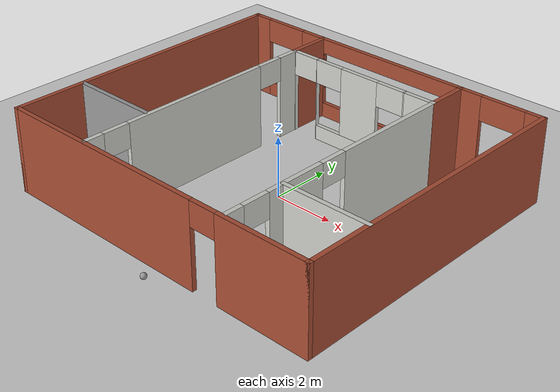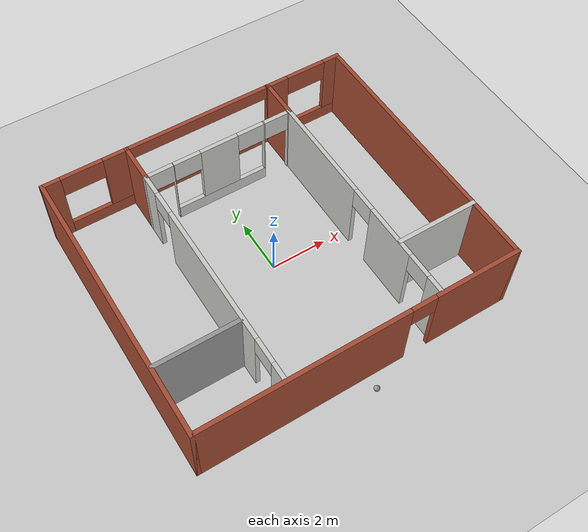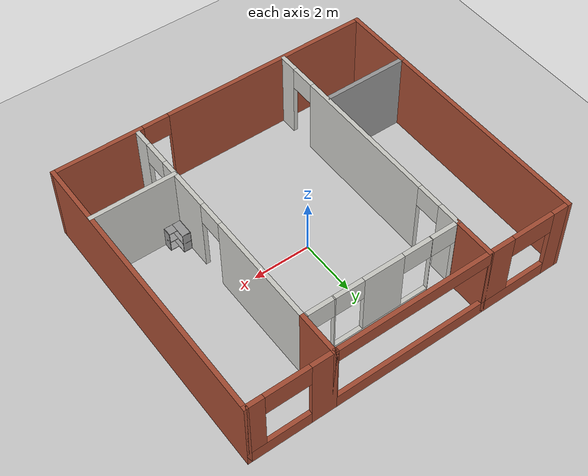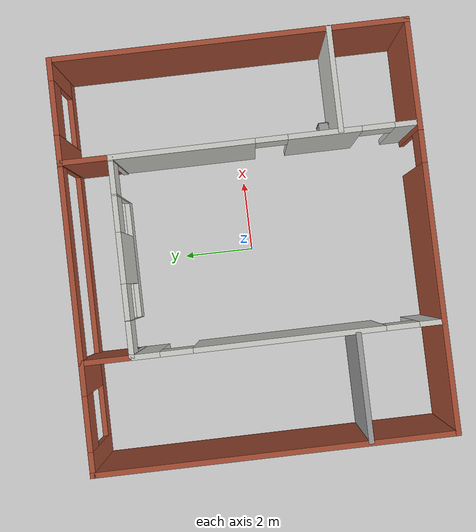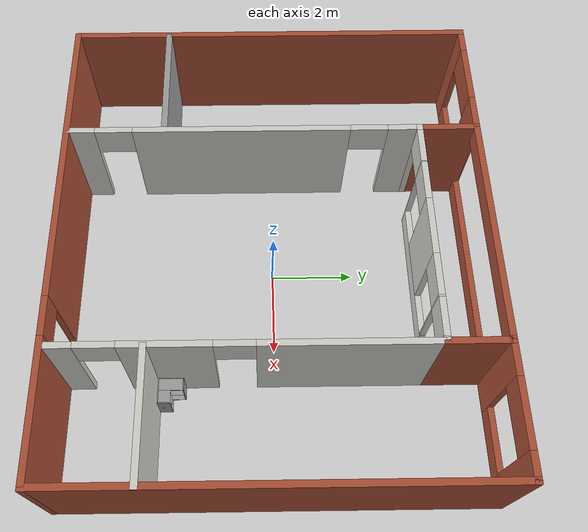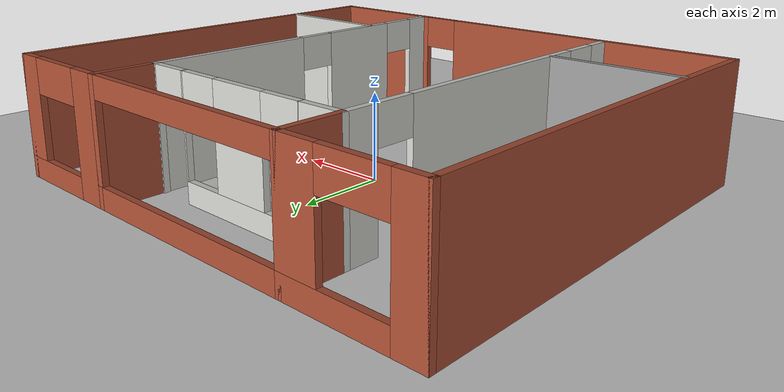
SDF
<sdf version="1.6">
 <world name="default">
  <plugin name="hello" filename="libhello.so"/>
  <light name="sun" type="directional">
   <pose>0 0 10 0 -0 0</pose>
   <diffuse>0.8 0.8 0.8 1</diffuse>
   <specular>0.2 0.2 0.2 1</specular>
   <attenuation>
    <range>1000</range>
    <constant>0.9</constant>
    <linear>0.01</linear>
    <quadratic>0.001</quadratic>
   </attenuation>
   <direction>-0.5 0.1 -0.9</direction>
  </light>
  <model name="ground_plane">
   <static>1</static>
   <link name="link">
    <collision name="collision">
     <geometry><plane><normal>0 0 1</normal><size>100 100</size></plane></geometry>
     <surface>
      <contact><collide_bitmask>65535</collide_bitmask></contact>
      <friction><ode><mu>100</mu><mu2>50</mu2></ode></friction>
     </surface>
    </collision>
    <visual name="visual">
     <cast_shadows>0</cast_shadows>
     <geometry><plane><normal>0 0 1</normal><size>100 100</size></plane></geometry>
     <material>
      <script><uri>file://media/materials/scripts/gazebo.material</uri><name>Gazebo/Grey</name></script>
     </material>
    </visual>
   </link>
  </model>
  <gravity>0 0 -9.8</gravity>
  <magnetic_field>6e-06 2.3e-05 -4.2e-05</magnetic_field>
  <atmosphere type="adiabatic"/>
  <physics name="default_physics" default="0" type="ode">
   <max_step_size>0.001</max_step_size>
   <real_time_factor>1</real_time_factor>
   <real_time_update_rate>1000</real_time_update_rate>
  </physics>
  <scene><ambient>0.4 0.4 0.4 1</ambient><background>0.7 0.7 0.7 1</background><shadows>1</shadows></scene>
  <spherical_coordinates>
   <surface_model>EARTH_WGS84</surface_model>
   <latitude_deg>0</latitude_deg>
   <longitude_deg>0</longitude_deg>
   <elevation>0</elevation>
   <heading_deg>0</heading_deg>
  </spherical_coordinates>
  <model name="my_ball">
   <link name="link_0">
    <inertial>
     <mass>1</mass>
     <inertia><ixx>0.1</ixx><ixy>0</ixy><ixz>0</ixz><iyy>0.1</iyy><iyz>0</iyz><izz>0.1</izz></inertia>
    </inertial>
    <visual name="visual">
     <geometry><sphere><radius>0.1</radius></sphere></geometry>
     <material>
      <lighting>1</lighting>
      <script><uri>file://media/materials/scripts/gazebo.material</uri><name>Gazebo/Grey</name></script>
      <shader type="pixel"><normal_map>__default__</normal_map></shader>
      <ambient>1 1 1 1</ambient>
      <diffuse>1 1 1 1</diffuse>
      <specular>1 1 1 1</specular>
      <emissive>1 1 1 1</emissive>
     </material>
    </visual>
    <collision name="collision">
     <geometry><sphere><radius>0.1</radius></sphere></geometry>
     <surface>
      <friction>
       <ode><mu>1</mu><mu2>1</mu2><fdir1>0 0 0</fdir1><slip1>0</slip1><slip2>0</slip2></ode>
       <torsional>
        <coefficient>1</coefficient>
        <patch_radius>0</patch_radius>
        <surface_radius>0</surface_radius>
        <use_patch_radius>1</use_patch_radius>
        <ode><slip>0</slip></ode>
       </torsional>
      </friction>
      <bounce><restitution_coefficient>0</restitution_coefficient><threshold>1e+06</threshold></bounce>
      <contact>
       <collide_without_contact>0</collide_without_contact>
       <collide_without_contact_bitmask>1</collide_without_contact_bitmask>
       <collide_bitmask>1</collide_bitmask>
       <ode>
        <soft_cfm>0</soft_cfm>
        <soft_erp>0.2</soft_erp>
        <kp>1e+13</kp>
        <kd>1</kd>
        <max_vel>0.01</max_vel>
        <min_depth>0</min_depth>
       </ode>
       <bullet>
        <split_impulse>1</split_impulse>
        <split_impulse_penetration_threshold>-0.01</split_impulse_penetration_threshold>
        <soft_cfm>0</soft_cfm>
        <soft_erp>0.2</soft_erp>
        <kp>1e+13</kp>
        <kd>1</kd>
       </bullet>
      </contact>
     </surface>
    </collision>
   </link>
   <static>0</static>
   <pose>0.318591 -5.49363 0.1 0 -0 0</pose>
  </model>
  <plugin name="collision_map_creator" filename="libcollision_map_creator.so"/>
  <model name="house">
   <link name="Wall_12">
    <pose>-2.65056 4.228 0 0 0 -1.5708</pose>
    <visual name="Wall_12_Visual">
     <pose>0 0 1.4 0 -0 0</pose>
     <geometry><box><size>1.5 0.15 2.8</size></box></geometry>
     <material>
      <script><uri>file://media/materials/scripts/gazebo.material</uri><name>Gazebo/Bricks</name></script>
      <ambient>1 1 1 1</ambient>
      <shader type="pixel"/>
      <diffuse>1 1 1 1</diffuse>
      <specular>0.2 0.2 0.2 1</specular>
      <emissive>0 0 0 1</emissive>
     </material>
     <meta><layer>0</layer></meta>
    </visual>
    <collision name="Wall_12_Collision">
     <pose>0 0 1.4 0 -0 0</pose>
     <geometry><box><size>1.5 0.15 2.8</size></box></geometry>
     <surface>
      <friction>
       <ode><mu>1</mu><mu2>1</mu2><fdir1>0 0 0</fdir1><slip1>0</slip1><slip2>0</slip2></ode>
       <torsional>
        <coefficient>1</coefficient>
        <patch_radius>0</patch_radius>
        <surface_radius>0</surface_radius>
        <use_patch_radius>1</use_patch_radius>
        <ode><slip>0</slip></ode>
       </torsional>
      </friction>
      <bounce><restitution_coefficient>0</restitution_coefficient><threshold>1e+06</threshold></bounce>
      <contact>
       <collide_without_contact>0</collide_without_contact>
       <collide_without_contact_bitmask>1</collide_without_contact_bitmask>
       <collide_bitmask>1</collide_bitmask>
       <ode>
        <soft_cfm>0</soft_cfm>
        <soft_erp>0.2</soft_erp>
        <kp>1e+13</kp>
        <kd>1</kd>
        <max_vel>0.01</max_vel>
        <min_depth>0</min_depth>
       </ode>
       <bullet>
        <split_impulse>1</split_impulse>
        <split_impulse_penetration_threshold>-0.01</split_impulse_penetration_threshold>
        <soft_cfm>0</soft_cfm>
        <soft_erp>0.2</soft_erp>
        <kp>1e+13</kp>
        <kd>1</kd>
       </bullet>
      </contact>
     </surface>
    </collision>
   </link>
   <link name="Wall_14">
    <pose>0.040444 3.553 0 0 -0 0</pose>
    <visual name="Wall_14_Visual_0">
     <pose>-2.6865 0 1.4 0 -0 0</pose>
     <geometry><box><size>0.159462 0.15 2.8</size></box></geometry>
     <material>
      <script><uri>file://media/materials/scripts/gazebo.material</uri><name>Gazebo/CeilingTiled</name></script>
      <ambient>1 1 1 1</ambient>
      <shader type="pixel"/>
      <diffuse>1 1 1 1</diffuse>
      <specular>0 0 0 1</specular>
      <emissive>0 0 0 1</emissive>
     </material>
     <meta><layer>0</layer></meta>
    </visual>
    <visual name="Wall_14_Visual_1">
     <pose>-1.70025 0 1.4 0 -0 0</pose>
     <geometry><box><size>0.013045 0.15 2.8</size></box></geometry>
     <material>
      <script><uri>file://media/materials/scripts/gazebo.material</uri><name>Gazebo/CeilingTiled</name></script>
      <ambient>1 1 1 1</ambient>
      <shader type="pixel"/>
      <diffuse>1 1 1 1</diffuse>
      <specular>0 0 0 1</specular>
      <emissive>0 0 0 1</emissive>
     </material>
     <meta><layer>0</layer></meta>
    </visual>
    <visual name="Wall_14_Visual_2">
     <pose>2.70996 0 1.4 0 -0 0</pose>
     <geometry><box><size>0.112546 0.15 2.8</size></box></geometry>
     <material>
      <script><uri>file://media/materials/scripts/gazebo.material</uri><name>Gazebo/CeilingTiled</name></script>
      <ambient>1 1 1 1</ambient>
      <shader type="pixel"/>
      <diffuse>1 1 1 1</diffuse>
      <specular>0 0 0 1</specular>
      <emissive>0 0 0 1</emissive>
     </material>
     <meta><layer>0</layer></meta>
    </visual>
    <visual name="Wall_14_Visual_6">
     <pose>0.010082 0 1.65 0 -0 0</pose>
     <geometry><box><size>1.40761 0.15 2.3</size></box></geometry>
     <material>
      <script><uri>file://media/materials/scripts/gazebo.material</uri><name>Gazebo/CeilingTiled</name></script>
      <ambient>1 1 1 1</ambient>
      <shader type="pixel"/>
      <diffuse>1 1 1 1</diffuse>
      <specular>0 0 0 1</specular>
      <emissive>0 0 0 1</emissive>
     </material>
     <meta><layer>0</layer></meta>
    </visual>
    <visual name="Wall_14_Visual_4">
     <pose>0.029981 0 0.25 0 -0 0</pose>
     <geometry><box><size>3.44741 0.15 0.5</size></box></geometry>
     <material>
      <script><uri>file://media/materials/scripts/gazebo.material</uri><name>Gazebo/CeilingTiled</name></script>
      <ambient>1 1 1 1</ambient>
      <shader type="pixel"/>
      <diffuse>1 1 1 1</diffuse>
      <specular>0 0 0 1</specular>
      <emissive>0 0 0 1</emissive>
     </material>
     <meta><layer>0</layer></meta>
    </visual>
    <visual name="Wall_14_Visual_7">
     <pose>1.73379 0 1.65 0 -0 0</pose>
     <geometry><box><size>0.039797 0.15 2.3</size></box></geometry>
     <material>
      <script><uri>file://media/materials/scripts/gazebo.material</uri><name>Gazebo/CeilingTiled</name></script>
      <ambient>1 1 1 1</ambient>
      <shader type="pixel"/>
      <diffuse>1 1 1 1</diffuse>
      <specular>0 0 0 1</specular>
      <emissive>0 0 0 1</emissive>
     </material>
     <meta><layer>0</layer></meta>
    </visual>
    <visual name="Wall_14_Visual_9">
     <pose>-1.19372 0 2.4 0 -0 0</pose>
     <geometry><box><size>1 0.15 0.8</size></box></geometry>
     <material>
      <script><uri>file://media/materials/scripts/gazebo.material</uri><name>Gazebo/CeilingTiled</name></script>
      <ambient>1 1 1 1</ambient>
      <shader type="pixel"/>
      <diffuse>1 1 1 1</diffuse>
      <specular>0 0 0 1</specular>
      <emissive>0 0 0 1</emissive>
     </material>
     <meta><layer>0</layer></meta>
    </visual>
    <visual name="Wall_14_Visual_10">
     <pose>-2.15677 0 2.4 0 -0 0</pose>
     <geometry><box><size>0.9 0.15 0.8</size></box></geometry>
     <material>
      <script><uri>file://media/materials/scripts/gazebo.material</uri><name>Gazebo/CeilingTiled</name></script>
      <ambient>1 1 1 1</ambient>
      <shader type="pixel"/>
      <diffuse>1 1 1 1</diffuse>
      <specular>0 0 0 1</specular>
      <emissive>0 0 0 1</emissive>
     </material>
     <meta><layer>0</layer></meta>
    </visual>
    <visual name="Wall_14_Visual_11">
     <pose>1.21389 0 2.4 0 -0 0</pose>
     <geometry><box><size>1 0.15 0.8</size></box></geometry>
     <material>
      <script><uri>file://media/materials/scripts/gazebo.material</uri><name>Gazebo/CeilingTiled</name></script>
      <ambient>1 1 1 1</ambient>
      <shader type="pixel"/>
      <diffuse>1 1 1 1</diffuse>
      <specular>0 0 0 1</specular>
      <emissive>0 0 0 1</emissive>
     </material>
     <meta><layer>0</layer></meta>
    </visual>
    <visual name="Wall_14_Visual_12">
     <pose>2.20369 0 2.4 0 -0 0</pose>
     <geometry><box><size>0.9 0.15 0.8</size></box></geometry>
     <material>
      <script><uri>file://media/materials/scripts/gazebo.material</uri><name>Gazebo/CeilingTiled</name></script>
      <ambient>1 1 1 1</ambient>
      <shader type="pixel"/>
      <diffuse>1 1 1 1</diffuse>
      <specular>0 0 0 1</specular>
      <emissive>0 0 0 1</emissive>
     </material>
     <meta><layer>0</layer></meta>
    </visual>
    <collision name="Wall_14_Collision_0">
     <pose>-2.6865 0 1.4 0 -0 0</pose>
     <geometry><box><size>0.159462 0.15 2.8</size></box></geometry>
     <surface>
      <friction>
       <ode><mu>1</mu><mu2>1</mu2><fdir1>0 0 0</fdir1><slip1>0</slip1><slip2>0</slip2></ode>
       <torsional>
        <coefficient>1</coefficient>
        <patch_radius>0</patch_radius>
        <surface_radius>0</surface_radius>
        <use_patch_radius>1</use_patch_radius>
        <ode><slip>0</slip></ode>
       </torsional>
      </friction>
      <bounce><restitution_coefficient>0</restitution_coefficient><threshold>1e+06</threshold></bounce>
      <contact>
       <collide_without_contact>0</collide_without_contact>
       <collide_without_contact_bitmask>1</collide_without_contact_bitmask>
       <collide_bitmask>1</collide_bitmask>
       <ode>
        <soft_cfm>0</soft_cfm>
        <soft_erp>0.2</soft_erp>
        <kp>1e+13</kp>
        <kd>1</kd>
        <max_vel>0.01</max_vel>
        <min_depth>0</min_depth>
       </ode>
       <bullet>
        <split_impulse>1</split_impulse>
        <split_impulse_penetration_threshold>-0.01</split_impulse_penetration_threshold>
        <soft_cfm>0</soft_cfm>
        <soft_erp>0.2</soft_erp>
        <kp>1e+13</kp>
        <kd>1</kd>
       </bullet>
      </contact>
     </surface>
    </collision>
    <collision name="Wall_14_Collision_1">
     <pose>-1.70025 0 1.4 0 -0 0</pose>
     <geometry><box><size>0.013045 0.15 2.8</size></box></geometry>
     <surface>
      <friction>
       <ode><mu>1</mu><mu2>1</mu2><fdir1>0 0 0</fdir1><slip1>0</slip1><slip2>0</slip2></ode>
       <torsional>
        <coefficient>1</coefficient>
        <patch_radius>0</patch_radius>
        <surface_radius>0</surface_radius>
        <use_patch_radius>1</use_patch_radius>
        <ode><slip>0</slip></ode>
       </torsional>
      </friction>
      <bounce><restitution_coefficient>0</restitution_coefficient><threshold>1e+06</threshold></bounce>
      <contact>
       <collide_without_contact>0</collide_without_contact>
       <collide_without_contact_bitmask>1</collide_without_contact_bitmask>
       <collide_bitmask>1</collide_bitmask>
       <ode>
        <soft_cfm>0</soft_cfm>
        <soft_erp>0.2</soft_erp>
        <kp>1e+13</kp>
        <kd>1</kd>
        <max_vel>0.01</max_vel>
        <min_depth>0</min_depth>
       </ode>
       <bullet>
        <split_impulse>1</split_impulse>
        <split_impulse_penetration_threshold>-0.01</split_impulse_penetration_threshold>
        <soft_cfm>0</soft_cfm>
        <soft_erp>0.2</soft_erp>
        <kp>1e+13</kp>
        <kd>1</kd>
       </bullet>
      </contact>
     </surface>
    </collision>
    <collision name="Wall_14_Collision_4">
     <pose>0.029981 0 0.25 0 -0 0</pose>
     <geometry><box><size>3.44741 0.15 0.5</size></box></geometry>
     <surface>
      <friction>
       <ode><mu>1</mu><mu2>1</mu2><fdir1>0 0 0</fdir1><slip1>0</slip1><slip2>0</slip2></ode>
       <torsional>
        <coefficient>1</coefficient>
        <patch_radius>0</patch_radius>
        <surface_radius>0</surface_radius>
        <use_patch_radius>1</use_patch_radius>
        <ode><slip>0</slip></ode>
       </torsional>
      </friction>
      <bounce><restitution_coefficient>0</restitution_coefficient><threshold>1e+06</threshold></bounce>
      <contact>
       <collide_without_contact>0</collide_without_contact>
       <collide_without_contact_bitmask>1</collide_without_contact_bitmask>
       <collide_bitmask>1</collide_bitmask>
       <ode>
        <soft_cfm>0</soft_cfm>
        <soft_erp>0.2</soft_erp>
        <kp>1e+13</kp>
        <kd>1</kd>
        <max_vel>0.01</max_vel>
        <min_depth>0</min_depth>
       </ode>
       <bullet>
        <split_impulse>1</split_impulse>
        <split_impulse_penetration_threshold>-0.01</split_impulse_penetration_threshold>
        <soft_cfm>0</soft_cfm>
        <soft_erp>0.2</soft_erp>
        <kp>1e+13</kp>
        <kd>1</kd>
       </bullet>
      </contact>
     </surface>
    </collision>
    <collision name="Wall_14_Collision_2">
     <pose>2.70996 0 1.4 0 -0 0</pose>
     <geometry><box><size>0.112546 0.15 2.8</size></box></geometry>
     <surface>
      <friction>
       <ode><mu>1</mu><mu2>1</mu2><fdir1>0 0 0</fdir1><slip1>0</slip1><slip2>0</slip2></ode>
       <torsional>
        <coefficient>1</coefficient>
        <patch_radius>0</patch_radius>
        <surface_radius>0</surface_radius>
        <use_patch_radius>1</use_patch_radius>
        <ode><slip>0</slip></ode>
       </torsional>
      </friction>
      <bounce><restitution_coefficient>0</restitution_coefficient><threshold>1e+06</threshold></bounce>
      <contact>
       <collide_without_contact>0</collide_without_contact>
       <collide_without_contact_bitmask>1</collide_without_contact_bitmask>
       <collide_bitmask>1</collide_bitmask>
       <ode>
        <soft_cfm>0</soft_cfm>
        <soft_erp>0.2</soft_erp>
        <kp>1e+13</kp>
        <kd>1</kd>
        <max_vel>0.01</max_vel>
        <min_depth>0</min_depth>
       </ode>
       <bullet>
        <split_impulse>1</split_impulse>
        <split_impulse_penetration_threshold>-0.01</split_impulse_penetration_threshold>
        <soft_cfm>0</soft_cfm>
        <soft_erp>0.2</soft_erp>
        <kp>1e+13</kp>
        <kd>1</kd>
       </bullet>
      </contact>
     </surface>
    </collision>
    <collision name="Wall_14_Collision_6">
     <pose>0.010082 0 1.65 0 -0 0</pose>
     <geometry><box><size>1.40761 0.15 2.3</size></box></geometry>
     <surface>
      <friction>
       <ode><mu>1</mu><mu2>1</mu2><fdir1>0 0 0</fdir1><slip1>0</slip1><slip2>0</slip2></ode>
       <torsional>
        <coefficient>1</coefficient>
        <patch_radius>0</patch_radius>
        <surface_radius>0</surface_radius>
        <use_patch_radius>1</use_patch_radius>
        <ode><slip>0</slip></ode>
       </torsional>
      </friction>
      <bounce><restitution_coefficient>0</restitution_coefficient><threshold>1e+06</threshold></bounce>
      <contact>
       <collide_without_contact>0</collide_without_contact>
       <collide_without_contact_bitmask>1</collide_without_contact_bitmask>
       <collide_bitmask>1</collide_bitmask>
       <ode>
        <soft_cfm>0</soft_cfm>
        <soft_erp>0.2</soft_erp>
        <kp>1e+13</kp>
        <kd>1</kd>
        <max_vel>0.01</max_vel>
        <min_depth>0</min_depth>
       </ode>
       <bullet>
        <split_impulse>1</split_impulse>
        <split_impulse_penetration_threshold>-0.01</split_impulse_penetration_threshold>
        <soft_cfm>0</soft_cfm>
        <soft_erp>0.2</soft_erp>
        <kp>1e+13</kp>
        <kd>1</kd>
       </bullet>
      </contact>
     </surface>
    </collision>
    <collision name="Wall_14_Collision_7">
     <pose>1.73379 0 1.65 0 -0 0</pose>
     <geometry><box><size>0.039797 0.15 2.3</size></box></geometry>
     <surface>
      <friction>
       <ode><mu>1</mu><mu2>1</mu2><fdir1>0 0 0</fdir1><slip1>0</slip1><slip2>0</slip2></ode>
       <torsional>
        <coefficient>1</coefficient>
        <patch_radius>0</patch_radius>
        <surface_radius>0</surface_radius>
        <use_patch_radius>1</use_patch_radius>
        <ode><slip>0</slip></ode>
       </torsional>
      </friction>
      <bounce><restitution_coefficient>0</restitution_coefficient><threshold>1e+06</threshold></bounce>
      <contact>
       <collide_without_contact>0</collide_without_contact>
       <collide_without_contact_bitmask>1</collide_without_contact_bitmask>
       <collide_bitmask>1</collide_bitmask>
       <ode>
        <soft_cfm>0</soft_cfm>
        <soft_erp>0.2</soft_erp>
        <kp>1e+13</kp>
        <kd>1</kd>
        <max_vel>0.01</max_vel>
        <min_depth>0</min_depth>
       </ode>
       <bullet>
        <split_impulse>1</split_impulse>
        <split_impulse_penetration_threshold>-0.01</split_impulse_penetration_threshold>
        <soft_cfm>0</soft_cfm>
        <soft_erp>0.2</soft_erp>
        <kp>1e+13</kp>
        <kd>1</kd>
       </bullet>
      </contact>
     </surface>
    </collision>
    <collision name="Wall_14_Collision_9">
     <pose>-1.19372 0 2.4 0 -0 0</pose>
     <geometry><box><size>1 0.15 0.8</size></box></geometry>
     <surface>
      <friction>
       <ode><mu>1</mu><mu2>1</mu2><fdir1>0 0 0</fdir1><slip1>0</slip1><slip2>0</slip2></ode>
       <torsional>
        <coefficient>1</coefficient>
        <patch_radius>0</patch_radius>
        <surface_radius>0</surface_radius>
        <use_patch_radius>1</use_patch_radius>
        <ode><slip>0</slip></ode>
       </torsional>
      </friction>
      <bounce><restitution_coefficient>0</restitution_coefficient><threshold>1e+06</threshold></bounce>
      <contact>
       <collide_without_contact>0</collide_without_contact>
       <collide_without_contact_bitmask>1</collide_without_contact_bitmask>
       <collide_bitmask>1</collide_bitmask>
       <ode>
        <soft_cfm>0</soft_cfm>
        <soft_erp>0.2</soft_erp>
        <kp>1e+13</kp>
        <kd>1</kd>
        <max_vel>0.01</max_vel>
        <min_depth>0</min_depth>
       </ode>
       <bullet>
        <split_impulse>1</split_impulse>
        <split_impulse_penetration_threshold>-0.01</split_impulse_penetration_threshold>
        <soft_cfm>0</soft_cfm>
        <soft_erp>0.2</soft_erp>
        <kp>1e+13</kp>
        <kd>1</kd>
       </bullet>
      </contact>
     </surface>
    </collision>
    <collision name="Wall_14_Collision_12">
     <pose>2.20369 0 2.4 0 -0 0</pose>
     <geometry><box><size>0.9 0.15 0.8</size></box></geometry>
     <surface>
      <friction>
       <ode><mu>1</mu><mu2>1</mu2><fdir1>0 0 0</fdir1><slip1>0</slip1><slip2>0</slip2></ode>
       <torsional>
        <coefficient>1</coefficient>
        <patch_radius>0</patch_radius>
        <surface_radius>0</surface_radius>
        <use_patch_radius>1</use_patch_radius>
        <ode><slip>0</slip></ode>
       </torsional>
      </friction>
      <bounce><restitution_coefficient>0</restitution_coefficient><threshold>1e+06</threshold></bounce>
      <contact>
       <collide_without_contact>0</collide_without_contact>
       <collide_without_contact_bitmask>1</collide_without_contact_bitmask>
       <collide_bitmask>1</collide_bitmask>
       <ode>
        <soft_cfm>0</soft_cfm>
        <soft_erp>0.2</soft_erp>
        <kp>1e+13</kp>
        <kd>1</kd>
        <max_vel>0.01</max_vel>
        <min_depth>0</min_depth>
       </ode>
       <bullet>
        <split_impulse>1</split_impulse>
        <split_impulse_penetration_threshold>-0.01</split_impulse_penetration_threshold>
        <soft_cfm>0</soft_cfm>
        <soft_erp>0.2</soft_erp>
        <kp>1e+13</kp>
        <kd>1</kd>
       </bullet>
      </contact>
     </surface>
    </collision>
    <collision name="Wall_14_Collision_10">
     <pose>-2.15677 0 2.4 0 -0 0</pose>
     <geometry><box><size>0.9 0.15 0.8</size></box></geometry>
     <surface>
      <friction>
       <ode><mu>1</mu><mu2>1</mu2><fdir1>0 0 0</fdir1><slip1>0</slip1><slip2>0</slip2></ode>
       <torsional>
        <coefficient>1</coefficient>
        <patch_radius>0</patch_radius>
        <surface_radius>0</surface_radius>
        <use_patch_radius>1</use_patch_radius>
        <ode><slip>0</slip></ode>
       </torsional>
      </friction>
      <bounce><restitution_coefficient>0</restitution_coefficient><threshold>1e+06</threshold></bounce>
      <contact>
       <collide_without_contact>0</collide_without_contact>
       <collide_without_contact_bitmask>1</collide_without_contact_bitmask>
       <collide_bitmask>1</collide_bitmask>
       <ode>
        <soft_cfm>0</soft_cfm>
        <soft_erp>0.2</soft_erp>
        <kp>1e+13</kp>
        <kd>1</kd>
        <max_vel>0.01</max_vel>
        <min_depth>0</min_depth>
       </ode>
       <bullet>
        <split_impulse>1</split_impulse>
        <split_impulse_penetration_threshold>-0.01</split_impulse_penetration_threshold>
        <soft_cfm>0</soft_cfm>
        <soft_erp>0.2</soft_erp>
        <kp>1e+13</kp>
        <kd>1</kd>
       </bullet>
      </contact>
     </surface>
    </collision>
    <collision name="Wall_14_Collision_11">
     <pose>1.21389 0 2.4 0 -0 0</pose>
     <geometry><box><size>1 0.15 0.8</size></box></geometry>
     <surface>
      <friction>
       <ode><mu>1</mu><mu2>1</mu2><fdir1>0 0 0</fdir1><slip1>0</slip1><slip2>0</slip2></ode>
       <torsional>
        <coefficient>1</coefficient>
        <patch_radius>0</patch_radius>
        <surface_radius>0</surface_radius>
        <use_patch_radius>1</use_patch_radius>
        <ode><slip>0</slip></ode>
       </torsional>
      </friction>
      <bounce><restitution_coefficient>0</restitution_coefficient><threshold>1e+06</threshold></bounce>
      <contact>
       <collide_without_contact>0</collide_without_contact>
       <collide_without_contact_bitmask>1</collide_without_contact_bitmask>
       <collide_bitmask>1</collide_bitmask>
       <ode>
        <soft_cfm>0</soft_cfm>
        <soft_erp>0.2</soft_erp>
        <kp>1e+13</kp>
        <kd>1</kd>
        <max_vel>0.01</max_vel>
        <min_depth>0</min_depth>
       </ode>
       <bullet>
        <split_impulse>1</split_impulse>
        <split_impulse_penetration_threshold>-0.01</split_impulse_penetration_threshold>
        <soft_cfm>0</soft_cfm>
        <soft_erp>0.2</soft_erp>
        <kp>1e+13</kp>
        <kd>1</kd>
       </bullet>
      </contact>
     </surface>
    </collision>
   </link>
   <link name="Wall_2">
    <pose>-4.15056 4.925 0 0 -0 0</pose>
    <visual name="Wall_2_Visual_0">
     <pose>-1.22601 0 1.4 0 -0 0</pose>
     <geometry><box><size>0.697976 0.15 2.8</size></box></geometry>
     <material>
      <script><uri>file://media/materials/scripts/gazebo.material</uri><name>Gazebo/Bricks</name></script>
      <ambient>1 1 1 1</ambient>
      <shader type="pixel"/>
      <diffuse>1 1 1 1</diffuse>
      <specular>0.2 0.2 0.2 1</specular>
      <emissive>0 0 0 1</emissive>
     </material>
     <meta><layer>0</layer></meta>
    </visual>
    <visual name="Wall_2_Visual_2">
     <pose>1.09899 0 1.65 0 -0 0</pose>
     <geometry><box><size>0.952024 0.15 2.3</size></box></geometry>
     <material>
      <script><uri>file://media/materials/scripts/gazebo.material</uri><name>Gazebo/Bricks</name></script>
      <ambient>1 1 1 1</ambient>
      <shader type="pixel"/>
      <diffuse>1 1 1 1</diffuse>
      <specular>0.2 0.2 0.2 1</specular>
      <emissive>0 0 0 1</emissive>
     </material>
     <meta><layer>0</layer></meta>
    </visual>
    <visual name="Wall_2_Visual_1">
     <pose>0.348988 0 0.25 0 -0 0</pose>
     <geometry><box><size>2.45202 0.15 0.5</size></box></geometry>
     <material>
      <script><uri>file://media/materials/scripts/gazebo.material</uri><name>Gazebo/Bricks</name></script>
      <ambient>1 1 1 1</ambient>
      <shader type="pixel"/>
      <diffuse>1 1 1 1</diffuse>
      <specular>0.2 0.2 0.2 1</specular>
      <emissive>0 0 0 1</emissive>
     </material>
     <meta><layer>0</layer></meta>
    </visual>
    <visual name="Wall_2_Visual_3">
     <pose>-0.127024 0 2.4 0 -0 0</pose>
     <geometry><box><size>1.5 0.15 0.8</size></box></geometry>
     <material>
      <script><uri>file://media/materials/scripts/gazebo.material</uri><name>Gazebo/Bricks</name></script>
      <ambient>1 1 1 1</ambient>
      <shader type="pixel"/>
      <diffuse>1 1 1 1</diffuse>
      <specular>0.2 0.2 0.2 1</specular>
      <emissive>0 0 0 1</emissive>
     </material>
     <meta><layer>0</layer></meta>
    </visual>
    <collision name="Wall_2_Collision_1">
     <pose>0.348988 0 0.25 0 -0 0</pose>
     <geometry><box><size>2.45202 0.15 0.5</size></box></geometry>
     <surface>
      <friction>
       <ode><mu>1</mu><mu2>1</mu2><fdir1>0 0 0</fdir1><slip1>0</slip1><slip2>0</slip2></ode>
       <torsional>
        <coefficient>1</coefficient>
        <patch_radius>0</patch_radius>
        <surface_radius>0</surface_radius>
        <use_patch_radius>1</use_patch_radius>
        <ode><slip>0</slip></ode>
       </torsional>
      </friction>
      <bounce><restitution_coefficient>0</restitution_coefficient><threshold>1e+06</threshold></bounce>
      <contact>
       <collide_without_contact>0</collide_without_contact>
       <collide_without_contact_bitmask>1</collide_without_contact_bitmask>
       <collide_bitmask>1</collide_bitmask>
       <ode>
        <soft_cfm>0</soft_cfm>
        <soft_erp>0.2</soft_erp>
        <kp>1e+13</kp>
        <kd>1</kd>
        <max_vel>0.01</max_vel>
        <min_depth>0</min_depth>
       </ode>
       <bullet>
        <split_impulse>1</split_impulse>
        <split_impulse_penetration_threshold>-0.01</split_impulse_penetration_threshold>
        <soft_cfm>0</soft_cfm>
        <soft_erp>0.2</soft_erp>
        <kp>1e+13</kp>
        <kd>1</kd>
       </bullet>
      </contact>
     </surface>
    </collision>
    <collision name="Wall_2_Collision_2">
     <pose>1.09899 0 1.65 0 -0 0</pose>
     <geometry><box><size>0.952024 0.15 2.3</size></box></geometry>
     <surface>
      <friction>
       <ode><mu>1</mu><mu2>1</mu2><fdir1>0 0 0</fdir1><slip1>0</slip1><slip2>0</slip2></ode>
       <torsional>
        <coefficient>1</coefficient>
        <patch_radius>0</patch_radius>
        <surface_radius>0</surface_radius>
        <use_patch_radius>1</use_patch_radius>
        <ode><slip>0</slip></ode>
       </torsional>
      </friction>
      <bounce><restitution_coefficient>0</restitution_coefficient><threshold>1e+06</threshold></bounce>
      <contact>
       <collide_without_contact>0</collide_without_contact>
       <collide_without_contact_bitmask>1</collide_without_contact_bitmask>
       <collide_bitmask>1</collide_bitmask>
       <ode>
        <soft_cfm>0</soft_cfm>
        <soft_erp>0.2</soft_erp>
        <kp>1e+13</kp>
        <kd>1</kd>
        <max_vel>0.01</max_vel>
        <min_depth>0</min_depth>
       </ode>
       <bullet>
        <split_impulse>1</split_impulse>
        <split_impulse_penetration_threshold>-0.01</split_impulse_penetration_threshold>
        <soft_cfm>0</soft_cfm>
        <soft_erp>0.2</soft_erp>
        <kp>1e+13</kp>
        <kd>1</kd>
       </bullet>
      </contact>
     </surface>
    </collision>
    <collision name="Wall_2_Collision_0">
     <pose>-1.22601 0 1.4 0 -0 0</pose>
     <geometry><box><size>0.697976 0.15 2.8</size></box></geometry>
     <surface>
      <friction>
       <ode><mu>1</mu><mu2>1</mu2><fdir1>0 0 0</fdir1><slip1>0</slip1><slip2>0</slip2></ode>
       <torsional>
        <coefficient>1</coefficient>
        <patch_radius>0</patch_radius>
        <surface_radius>0</surface_radius>
        <use_patch_radius>1</use_patch_radius>
        <ode><slip>0</slip></ode>
       </torsional>
      </friction>
      <bounce><restitution_coefficient>0</restitution_coefficient><threshold>1e+06</threshold></bounce>
      <contact>
       <collide_without_contact>0</collide_without_contact>
       <collide_without_contact_bitmask>1</collide_without_contact_bitmask>
       <collide_bitmask>1</collide_bitmask>
       <ode>
        <soft_cfm>0</soft_cfm>
        <soft_erp>0.2</soft_erp>
        <kp>1e+13</kp>
        <kd>1</kd>
        <max_vel>0.01</max_vel>
        <min_depth>0</min_depth>
       </ode>
       <bullet>
        <split_impulse>1</split_impulse>
        <split_impulse_penetration_threshold>-0.01</split_impulse_penetration_threshold>
        <soft_cfm>0</soft_cfm>
        <soft_erp>0.2</soft_erp>
        <kp>1e+13</kp>
        <kd>1</kd>
       </bullet>
      </contact>
     </surface>
    </collision>
    <collision name="Wall_2_Collision_3">
     <pose>-0.127024 0 2.4 0 -0 0</pose>
     <geometry><box><size>1.5 0.15 0.8</size></box></geometry>
     <surface>
      <friction>
       <ode><mu>1</mu><mu2>1</mu2><fdir1>0 0 0</fdir1><slip1>0</slip1><slip2>0</slip2></ode>
       <torsional>
        <coefficient>1</coefficient>
        <patch_radius>0</patch_radius>
        <surface_radius>0</surface_radius>
        <use_patch_radius>1</use_patch_radius>
        <ode><slip>0</slip></ode>
       </torsional>
      </friction>
      <bounce><restitution_coefficient>0</restitution_coefficient><threshold>1e+06</threshold></bounce>
      <contact>
       <collide_without_contact>0</collide_without_contact>
       <collide_without_contact_bitmask>1</collide_without_contact_bitmask>
       <collide_bitmask>1</collide_bitmask>
       <ode>
        <soft_cfm>0</soft_cfm>
        <soft_erp>0.2</soft_erp>
        <kp>1e+13</kp>
        <kd>1</kd>
        <max_vel>0.01</max_vel>
        <min_depth>0</min_depth>
       </ode>
       <bullet>
        <split_impulse>1</split_impulse>
        <split_impulse_penetration_threshold>-0.01</split_impulse_penetration_threshold>
        <soft_cfm>0</soft_cfm>
        <soft_erp>0.2</soft_erp>
        <kp>1e+13</kp>
        <kd>1</kd>
       </bullet>
      </contact>
     </surface>
    </collision>
   </link>
   <link name="Wall_3">
    <pose>0.074445 4.925 0 0 -0 0</pose>
    <visual name="Wall_3_Visual_0">
     <pose>-2.76234 0 1.4 0 -0 0</pose>
     <geometry><box><size>0.07533 0.15 2.8</size></box></geometry>
     <material>
      <script><uri>file://media/materials/scripts/gazebo.material</uri><name>Gazebo/Bricks</name></script>
      <ambient>1 1 1 1</ambient>
      <shader type="pixel"/>
      <diffuse>1 1 1 1</diffuse>
      <specular>0.2 0.2 0.2 1</specular>
      <emissive>0 0 0 1</emissive>
     </material>
     <meta><layer>0</layer></meta>
    </visual>
    <visual name="Wall_3_Visual_2">
     <pose>2.71166 0 1.65 0 -0 0</pose>
     <geometry><box><size>0.17667 0.15 2.3</size></box></geometry>
     <material>
      <script><uri>file://media/materials/scripts/gazebo.material</uri><name>Gazebo/Bricks</name></script>
      <ambient>1 1 1 1</ambient>
      <shader type="pixel"/>
      <diffuse>1 1 1 1</diffuse>
      <specular>0.2 0.2 0.2 1</specular>
      <emissive>0 0 0 1</emissive>
     </material>
     <meta><layer>0</layer></meta>
    </visual>
    <visual name="Wall_3_Visual_1">
     <pose>0.037665 0 0.25 0 -0 0</pose>
     <geometry><box><size>5.52467 0.15 0.5</size></box></geometry>
     <material>
      <script><uri>file://media/materials/scripts/gazebo.material</uri><name>Gazebo/Bricks</name></script>
      <ambient>1 1 1 1</ambient>
      <shader type="pixel"/>
      <diffuse>1 1 1 1</diffuse>
      <specular>0.2 0.2 0.2 1</specular>
      <emissive>0 0 0 1</emissive>
     </material>
     <meta><layer>0</layer></meta>
    </visual>
    <visual name="Wall_3_Visual_3">
     <pose>-0.05067 0 2.55 0 -0 0</pose>
     <geometry><box><size>5.348 0.15 0.5</size></box></geometry>
     <material>
      <script><uri>file://media/materials/scripts/gazebo.material</uri><name>Gazebo/Bricks</name></script>
      <ambient>1 1 1 1</ambient>
      <shader type="pixel"/>
      <diffuse>1 1 1 1</diffuse>
      <specular>0.2 0.2 0.2 1</specular>
      <emissive>0 0 0 1</emissive>
     </material>
     <meta><layer>0</layer></meta>
    </visual>
    <collision name="Wall_3_Collision_0">
     <pose>-2.76234 0 1.4 0 -0 0</pose>
     <geometry><box><size>0.07533 0.15 2.8</size></box></geometry>
     <surface>
      <friction>
       <ode><mu>1</mu><mu2>1</mu2><fdir1>0 0 0</fdir1><slip1>0</slip1><slip2>0</slip2></ode>
       <torsional>
        <coefficient>1</coefficient>
        <patch_radius>0</patch_radius>
        <surface_radius>0</surface_radius>
        <use_patch_radius>1</use_patch_radius>
        <ode><slip>0</slip></ode>
       </torsional>
      </friction>
      <bounce><restitution_coefficient>0</restitution_coefficient><threshold>1e+06</threshold></bounce>
      <contact>
       <collide_without_contact>0</collide_without_contact>
       <collide_without_contact_bitmask>1</collide_without_contact_bitmask>
       <collide_bitmask>1</collide_bitmask>
       <ode>
        <soft_cfm>0</soft_cfm>
        <soft_erp>0.2</soft_erp>
        <kp>1e+13</kp>
        <kd>1</kd>
        <max_vel>0.01</max_vel>
        <min_depth>0</min_depth>
       </ode>
       <bullet>
        <split_impulse>1</split_impulse>
        <split_impulse_penetration_threshold>-0.01</split_impulse_penetration_threshold>
        <soft_cfm>0</soft_cfm>
        <soft_erp>0.2</soft_erp>
        <kp>1e+13</kp>
        <kd>1</kd>
       </bullet>
      </contact>
     </surface>
    </collision>
    <collision name="Wall_3_Collision_1">
     <pose>0.037665 0 0.25 0 -0 0</pose>
     <geometry><box><size>5.52467 0.15 0.5</size></box></geometry>
     <surface>
      <friction>
       <ode><mu>1</mu><mu2>1</mu2><fdir1>0 0 0</fdir1><slip1>0</slip1><slip2>0</slip2></ode>
       <torsional>
        <coefficient>1</coefficient>
        <patch_radius>0</patch_radius>
        <surface_radius>0</surface_radius>
        <use_patch_radius>1</use_patch_radius>
        <ode><slip>0</slip></ode>
       </torsional>
      </friction>
      <bounce><restitution_coefficient>0</restitution_coefficient><threshold>1e+06</threshold></bounce>
      <contact>
       <collide_without_contact>0</collide_without_contact>
       <collide_without_contact_bitmask>1</collide_without_contact_bitmask>
       <collide_bitmask>1</collide_bitmask>
       <ode>
        <soft_cfm>0</soft_cfm>
        <soft_erp>0.2</soft_erp>
        <kp>1e+13</kp>
        <kd>1</kd>
        <max_vel>0.01</max_vel>
        <min_depth>0</min_depth>
       </ode>
       <bullet>
        <split_impulse>1</split_impulse>
        <split_impulse_penetration_threshold>-0.01</split_impulse_penetration_threshold>
        <soft_cfm>0</soft_cfm>
        <soft_erp>0.2</soft_erp>
        <kp>1e+13</kp>
        <kd>1</kd>
       </bullet>
      </contact>
     </surface>
    </collision>
    <collision name="Wall_3_Collision_2">
     <pose>2.71166 0 1.65 0 -0 0</pose>
     <geometry><box><size>0.17667 0.15 2.3</size></box></geometry>
     <surface>
      <friction>
       <ode><mu>1</mu><mu2>1</mu2><fdir1>0 0 0</fdir1><slip1>0</slip1><slip2>0</slip2></ode>
       <torsional>
        <coefficient>1</coefficient>
        <patch_radius>0</patch_radius>
        <surface_radius>0</surface_radius>
        <use_patch_radius>1</use_patch_radius>
        <ode><slip>0</slip></ode>
       </torsional>
      </friction>
      <bounce><restitution_coefficient>0</restitution_coefficient><threshold>1e+06</threshold></bounce>
      <contact>
       <collide_without_contact>0</collide_without_contact>
       <collide_without_contact_bitmask>1</collide_without_contact_bitmask>
       <collide_bitmask>1</collide_bitmask>
       <ode>
        <soft_cfm>0</soft_cfm>
        <soft_erp>0.2</soft_erp>
        <kp>1e+13</kp>
        <kd>1</kd>
        <max_vel>0.01</max_vel>
        <min_depth>0</min_depth>
       </ode>
       <bullet>
        <split_impulse>1</split_impulse>
        <split_impulse_penetration_threshold>-0.01</split_impulse_penetration_threshold>
        <soft_cfm>0</soft_cfm>
        <soft_erp>0.2</soft_erp>
        <kp>1e+13</kp>
        <kd>1</kd>
       </bullet>
      </contact>
     </surface>
    </collision>
    <collision name="Wall_3_Collision_3">
     <pose>-0.05067 0 2.55 0 -0 0</pose>
     <geometry><box><size>5.348 0.15 0.5</size></box></geometry>
     <surface>
      <friction>
       <ode><mu>1</mu><mu2>1</mu2><fdir1>0 0 0</fdir1><slip1>0</slip1><slip2>0</slip2></ode>
       <torsional>
        <coefficient>1</coefficient>
        <patch_radius>0</patch_radius>
        <surface_radius>0</surface_radius>
        <use_patch_radius>1</use_patch_radius>
        <ode><slip>0</slip></ode>
       </torsional>
      </friction>
      <bounce><restitution_coefficient>0</restitution_coefficient><threshold>1e+06</threshold></bounce>
      <contact>
       <collide_without_contact>0</collide_without_contact>
       <collide_without_contact_bitmask>1</collide_without_contact_bitmask>
       <collide_bitmask>1</collide_bitmask>
       <ode>
        <soft_cfm>0</soft_cfm>
        <soft_erp>0.2</soft_erp>
        <kp>1e+13</kp>
        <kd>1</kd>
        <max_vel>0.01</max_vel>
        <min_depth>0</min_depth>
       </ode>
       <bullet>
        <split_impulse>1</split_impulse>
        <split_impulse_penetration_threshold>-0.01</split_impulse_penetration_threshold>
        <soft_cfm>0</soft_cfm>
        <soft_erp>0.2</soft_erp>
        <kp>1e+13</kp>
        <kd>1</kd>
       </bullet>
      </contact>
     </surface>
    </collision>
   </link>
   <link name="Wall_36">
    <pose>2.79944 4.2395 0 0 0 -1.5708</pose>
    <visual name="Wall_36_Visual">
     <pose>0 0 1.4 0 -0 0</pose>
     <geometry><box><size>1.521 0.15 2.8</size></box></geometry>
     <material>
      <script><uri>file://media/materials/scripts/gazebo.material</uri><name>Gazebo/Bricks</name></script>
      <ambient>1 1 1 1</ambient>
      <shader type="pixel"/>
      <diffuse>1 1 1 1</diffuse>
      <specular>0.2 0.2 0.2 1</specular>
      <emissive>0 0 0 1</emissive>
     </material>
     <meta><layer>0</layer></meta>
    </visual>
    <collision name="Wall_36_Collision">
     <pose>0 0 1.4 0 -0 0</pose>
     <geometry><box><size>1.521 0.15 2.8</size></box></geometry>
     <surface>
      <friction>
       <ode><mu>1</mu><mu2>1</mu2><fdir1>0 0 0</fdir1><slip1>0</slip1><slip2>0</slip2></ode>
       <torsional>
        <coefficient>1</coefficient>
        <patch_radius>0</patch_radius>
        <surface_radius>0</surface_radius>
        <use_patch_radius>1</use_patch_radius>
        <ode><slip>0</slip></ode>
       </torsional>
      </friction>
      <bounce><restitution_coefficient>0</restitution_coefficient><threshold>1e+06</threshold></bounce>
      <contact>
       <collide_without_contact>0</collide_without_contact>
       <collide_without_contact_bitmask>1</collide_without_contact_bitmask>
       <collide_bitmask>1</collide_bitmask>
       <ode>
        <soft_cfm>0</soft_cfm>
        <soft_erp>0.2</soft_erp>
        <kp>1e+13</kp>
        <kd>1</kd>
        <max_vel>0.01</max_vel>
        <min_depth>0</min_depth>
       </ode>
       <bullet>
        <split_impulse>1</split_impulse>
        <split_impulse_penetration_threshold>-0.01</split_impulse_penetration_threshold>
        <soft_cfm>0</soft_cfm>
        <soft_erp>0.2</soft_erp>
        <kp>1e+13</kp>
        <kd>1</kd>
       </bullet>
      </contact>
     </surface>
    </collision>
   </link>
   <link name="Wall_4">
    <pose>4.22444 4.925 0 0 -0 0</pose>
    <visual name="Wall_4_Visual_0">
     <pose>-1.07575 0 1.4 0 -0 0</pose>
     <geometry><box><size>0.848504 0.15 2.8</size></box></geometry>
     <material>
      <script><uri>file://media/materials/scripts/gazebo.material</uri><name>Gazebo/Bricks</name></script>
      <ambient>1 1 1 1</ambient>
      <shader type="pixel"/>
      <diffuse>1 1 1 1</diffuse>
      <specular>0.2 0.2 0.2 1</specular>
      <emissive>0 0 0 1</emissive>
     </material>
     <meta><layer>0</layer></meta>
    </visual>
    <visual name="Wall_4_Visual_1">
     <pose>0.424252 0 0.25 0 -0 0</pose>
     <geometry><box><size>2.1515 0.15 0.5</size></box></geometry>
     <material>
      <script><uri>file://media/materials/scripts/gazebo.material</uri><name>Gazebo/Bricks</name></script>
      <ambient>1 1 1 1</ambient>
      <shader type="pixel"/>
      <diffuse>1 1 1 1</diffuse>
      <specular>0.2 0.2 0.2 1</specular>
      <emissive>0 0 0 1</emissive>
     </material>
     <meta><layer>0</layer></meta>
    </visual>
    <visual name="Wall_4_Visual_2">
     <pose>1.17425 0 1.65 0 -0 0</pose>
     <geometry><box><size>0.651496 0.15 2.3</size></box></geometry>
     <material>
      <script><uri>file://media/materials/scripts/gazebo.material</uri><name>Gazebo/Bricks</name></script>
      <ambient>1 1 1 1</ambient>
      <shader type="pixel"/>
      <diffuse>1 1 1 1</diffuse>
      <specular>0.2 0.2 0.2 1</specular>
      <emissive>0 0 0 1</emissive>
     </material>
     <meta><layer>0</layer></meta>
    </visual>
    <visual name="Wall_4_Visual_3">
     <pose>0.098504 0 2.4 0 -0 0</pose>
     <geometry><box><size>1.5 0.15 0.8</size></box></geometry>
     <material>
      <script><uri>file://media/materials/scripts/gazebo.material</uri><name>Gazebo/Bricks</name></script>
      <ambient>1 1 1 1</ambient>
      <shader type="pixel"/>
      <diffuse>1 1 1 1</diffuse>
      <specular>0.2 0.2 0.2 1</specular>
      <emissive>0 0 0 1</emissive>
     </material>
     <meta><layer>0</layer></meta>
    </visual>
    <collision name="Wall_4_Collision_0">
     <pose>-1.07575 0 1.4 0 -0 0</pose>
     <geometry><box><size>0.848504 0.15 2.8</size></box></geometry>
     <surface>
      <friction>
       <ode><mu>1</mu><mu2>1</mu2><fdir1>0 0 0</fdir1><slip1>0</slip1><slip2>0</slip2></ode>
       <torsional>
        <coefficient>1</coefficient>
        <patch_radius>0</patch_radius>
        <surface_radius>0</surface_radius>
        <use_patch_radius>1</use_patch_radius>
        <ode><slip>0</slip></ode>
       </torsional>
      </friction>
      <bounce><restitution_coefficient>0</restitution_coefficient><threshold>1e+06</threshold></bounce>
      <contact>
       <collide_without_contact>0</collide_without_contact>
       <collide_without_contact_bitmask>1</collide_without_contact_bitmask>
       <collide_bitmask>1</collide_bitmask>
       <ode>
        <soft_cfm>0</soft_cfm>
        <soft_erp>0.2</soft_erp>
        <kp>1e+13</kp>
        <kd>1</kd>
        <max_vel>0.01</max_vel>
        <min_depth>0</min_depth>
       </ode>
       <bullet>
        <split_impulse>1</split_impulse>
        <split_impulse_penetration_threshold>-0.01</split_impulse_penetration_threshold>
        <soft_cfm>0</soft_cfm>
        <soft_erp>0.2</soft_erp>
        <kp>1e+13</kp>
        <kd>1</kd>
       </bullet>
      </contact>
     </surface>
    </collision>
    <collision name="Wall_4_Collision_1">
     <pose>0.424252 0 0.25 0 -0 0</pose>
     <geometry><box><size>2.1515 0.15 0.5</size></box></geometry>
     <surface>
      <friction>
       <ode><mu>1</mu><mu2>1</mu2><fdir1>0 0 0</fdir1><slip1>0</slip1><slip2>0</slip2></ode>
       <torsional>
        <coefficient>1</coefficient>
        <patch_radius>0</patch_radius>
        <surface_radius>0</surface_radius>
        <use_patch_radius>1</use_patch_radius>
        <ode><slip>0</slip></ode>
       </torsional>
      </friction>
      <bounce><restitution_coefficient>0</restitution_coefficient><threshold>1e+06</threshold></bounce>
      <contact>
       <collide_without_contact>0</collide_without_contact>
       <collide_without_contact_bitmask>1</collide_without_contact_bitmask>
       <collide_bitmask>1</collide_bitmask>
       <ode>
        <soft_cfm>0</soft_cfm>
        <soft_erp>0.2</soft_erp>
        <kp>1e+13</kp>
        <kd>1</kd>
        <max_vel>0.01</max_vel>
        <min_depth>0</min_depth>
       </ode>
       <bullet>
        <split_impulse>1</split_impulse>
        <split_impulse_penetration_threshold>-0.01</split_impulse_penetration_threshold>
        <soft_cfm>0</soft_cfm>
        <soft_erp>0.2</soft_erp>
        <kp>1e+13</kp>
        <kd>1</kd>
       </bullet>
      </contact>
     </surface>
    </collision>
    <collision name="Wall_4_Collision_2">
     <pose>1.17425 0 1.65 0 -0 0</pose>
     <geometry><box><size>0.651496 0.15 2.3</size></box></geometry>
     <surface>
      <friction>
       <ode><mu>1</mu><mu2>1</mu2><fdir1>0 0 0</fdir1><slip1>0</slip1><slip2>0</slip2></ode>
       <torsional>
        <coefficient>1</coefficient>
        <patch_radius>0</patch_radius>
        <surface_radius>0</surface_radius>
        <use_patch_radius>1</use_patch_radius>
        <ode><slip>0</slip></ode>
       </torsional>
      </friction>
      <bounce><restitution_coefficient>0</restitution_coefficient><threshold>1e+06</threshold></bounce>
      <contact>
       <collide_without_contact>0</collide_without_contact>
       <collide_without_contact_bitmask>1</collide_without_contact_bitmask>
       <collide_bitmask>1</collide_bitmask>
       <ode>
        <soft_cfm>0</soft_cfm>
        <soft_erp>0.2</soft_erp>
        <kp>1e+13</kp>
        <kd>1</kd>
        <max_vel>0.01</max_vel>
        <min_depth>0</min_depth>
       </ode>
       <bullet>
        <split_impulse>1</split_impulse>
        <split_impulse_penetration_threshold>-0.01</split_impulse_penetration_threshold>
        <soft_cfm>0</soft_cfm>
        <soft_erp>0.2</soft_erp>
        <kp>1e+13</kp>
        <kd>1</kd>
       </bullet>
      </contact>
     </surface>
    </collision>
    <collision name="Wall_4_Collision_3">
     <pose>0.098504 0 2.4 0 -0 0</pose>
     <geometry><box><size>1.5 0.15 0.8</size></box></geometry>
     <surface>
      <friction>
       <ode><mu>1</mu><mu2>1</mu2><fdir1>0 0 0</fdir1><slip1>0</slip1><slip2>0</slip2></ode>
       <torsional>
        <coefficient>1</coefficient>
        <patch_radius>0</patch_radius>
        <surface_radius>0</surface_radius>
        <use_patch_radius>1</use_patch_radius>
        <ode><slip>0</slip></ode>
       </torsional>
      </friction>
      <bounce><restitution_coefficient>0</restitution_coefficient><threshold>1e+06</threshold></bounce>
      <contact>
       <collide_without_contact>0</collide_without_contact>
       <collide_without_contact_bitmask>1</collide_without_contact_bitmask>
       <collide_bitmask>1</collide_bitmask>
       <ode>
        <soft_cfm>0</soft_cfm>
        <soft_erp>0.2</soft_erp>
        <kp>1e+13</kp>
        <kd>1</kd>
        <max_vel>0.01</max_vel>
        <min_depth>0</min_depth>
       </ode>
       <bullet>
        <split_impulse>1</split_impulse>
        <split_impulse_penetration_threshold>-0.01</split_impulse_penetration_threshold>
        <soft_cfm>0</soft_cfm>
        <soft_erp>0.2</soft_erp>
        <kp>1e+13</kp>
        <kd>1</kd>
       </bullet>
      </contact>
     </surface>
    </collision>
   </link>
   <link name="Wall_41">
    <pose>2.79944 -0.621 0 0 -0 1.5708</pose>
    <inertial>
     <mass>1</mass>
     <inertia><ixx>1</ixx><ixy>0</ixy><ixz>0</ixz><iyy>1</iyy><iyz>0</iyz><izz>1</izz></inertia>
    </inertial>
    <visual name="Wall_41_Visual_0">
     <pose>-3.9395 0 1.4 0 -0 0</pose>
     <geometry><box><size>0.621 0.15 2.8</size></box></geometry>
     <material>
      <script><uri>file://media/materials/scripts/gazebo.material</uri><name>Gazebo/CeilingTiled</name></script>
      <ambient>1 1 1 1</ambient>
      <shader type="pixel"><normal_map>__default__</normal_map></shader>
      <diffuse>1 1 1 1</diffuse>
      <specular>0 0 0 1</specular>
      <emissive>0 0 0 1</emissive>
     </material>
     <meta><layer>0</layer></meta>
    </visual>
    <visual name="Wall_41_Visual_1">
     <pose>-1.71426 0 1.4 0 -0 0</pose>
     <geometry><box><size>2.02948 0.15 2.8</size></box></geometry>
     <material>
      <script><uri>file://media/materials/scripts/gazebo.material</uri><name>Gazebo/CeilingTiled</name></script>
      <ambient>1 1 1 1</ambient>
      <shader type="pixel"><normal_map>__default__</normal_map></shader>
      <diffuse>1 1 1 1</diffuse>
      <specular>0 0 0 1</specular>
      <emissive>0 0 0 1</emissive>
     </material>
     <meta><layer>0</layer></meta>
    </visual>
    <visual name="Wall_41_Visual_2">
     <pose>2.22524 0 1.4 0 -0 0</pose>
     <geometry><box><size>4.04952 0.15 2.8</size></box></geometry>
     <material>
      <script><uri>file://media/materials/scripts/gazebo.material</uri><name>Gazebo/CeilingTiled</name></script>
      <ambient>1 1 1 1</ambient>
      <shader type="pixel"><normal_map>__default__</normal_map></shader>
      <diffuse>1 1 1 1</diffuse>
      <specular>0 0 0 1</specular>
      <emissive>0 0 0 1</emissive>
     </material>
     <meta><layer>0</layer></meta>
    </visual>
    <visual name="Wall_41_Visual_5">
     <pose>-3.179 0 2.4 0 -0 0</pose>
     <geometry><box><size>0.9 0.15 0.8</size></box></geometry>
     <material>
      <script><uri>file://media/materials/scripts/gazebo.material</uri><name>Gazebo/CeilingTiled</name></script>
      <ambient>1 1 1 1</ambient>
      <shader type="pixel"><normal_map>__default__</normal_map></shader>
      <diffuse>1 1 1 1</diffuse>
      <specular>0 0 0 1</specular>
      <emissive>0 0 0 1</emissive>
     </material>
     <meta><layer>0</layer></meta>
    </visual>
    <visual name="Wall_41_Visual_6">
     <pose>-0.249524 0 2.4 0 -0 0</pose>
     <geometry><box><size>0.9 0.15 0.8</size></box></geometry>
     <material>
      <script><uri>file://media/materials/scripts/gazebo.material</uri><name>Gazebo/CeilingTiled</name></script>
      <ambient>1 1 1 1</ambient>
      <shader type="pixel"><normal_map>__default__</normal_map></shader>
      <diffuse>1 1 1 1</diffuse>
      <specular>0 0 0 1</specular>
      <emissive>0 0 0 1</emissive>
     </material>
     <meta><layer>0</layer></meta>
    </visual>
    <collision name="Wall_41_Collision_5">
     <pose>-3.179 0 2.4 0 -0 0</pose>
     <geometry><box><size>0.9 0.15 0.8</size></box></geometry>
     <surface>
      <friction>
       <ode><mu>1</mu><mu2>1</mu2><fdir1>0 0 0</fdir1><slip1>0</slip1><slip2>0</slip2></ode>
       <torsional>
        <coefficient>1</coefficient>
        <patch_radius>0</patch_radius>
        <surface_radius>0</surface_radius>
        <use_patch_radius>1</use_patch_radius>
        <ode><slip>0</slip></ode>
       </torsional>
      </friction>
      <bounce><restitution_coefficient>0</restitution_coefficient><threshold>1e+06</threshold></bounce>
      <contact>
       <collide_without_contact>0</collide_without_contact>
       <collide_without_contact_bitmask>1</collide_without_contact_bitmask>
       <collide_bitmask>1</collide_bitmask>
       <ode>
        <soft_cfm>0</soft_cfm>
        <soft_erp>0.2</soft_erp>
        <kp>1e+13</kp>
        <kd>1</kd>
        <max_vel>0.01</max_vel>
        <min_depth>0</min_depth>
       </ode>
       <bullet>
        <split_impulse>1</split_impulse>
        <split_impulse_penetration_threshold>-0.01</split_impulse_penetration_threshold>
        <soft_cfm>0</soft_cfm>
        <soft_erp>0.2</soft_erp>
        <kp>1e+13</kp>
        <kd>1</kd>
       </bullet>
      </contact>
     </surface>
    </collision>
    <collision name="Wall_41_Collision_0">
     <pose>-3.9395 0 1.4 0 -0 0</pose>
     <geometry><box><size>0.621 0.15 2.8</size></box></geometry>
     <surface>
      <friction>
       <ode><mu>1</mu><mu2>1</mu2><fdir1>0 0 0</fdir1><slip1>0</slip1><slip2>0</slip2></ode>
       <torsional>
        <coefficient>1</coefficient>
        <patch_radius>0</patch_radius>
        <surface_radius>0</surface_radius>
        <use_patch_radius>1</use_patch_radius>
        <ode><slip>0</slip></ode>
       </torsional>
      </friction>
      <bounce><restitution_coefficient>0</restitution_coefficient><threshold>1e+06</threshold></bounce>
      <contact>
       <collide_without_contact>0</collide_without_contact>
       <collide_without_contact_bitmask>1</collide_without_contact_bitmask>
       <collide_bitmask>1</collide_bitmask>
       <ode>
        <soft_cfm>0</soft_cfm>
        <soft_erp>0.2</soft_erp>
        <kp>1e+13</kp>
        <kd>1</kd>
        <max_vel>0.01</max_vel>
        <min_depth>0</min_depth>
       </ode>
       <bullet>
        <split_impulse>1</split_impulse>
        <split_impulse_penetration_threshold>-0.01</split_impulse_penetration_threshold>
        <soft_cfm>0</soft_cfm>
        <soft_erp>0.2</soft_erp>
        <kp>1e+13</kp>
        <kd>1</kd>
       </bullet>
      </contact>
     </surface>
    </collision>
    <collision name="Wall_41_Collision_2">
     <pose>2.22524 0 1.4 0 -0 0</pose>
     <geometry><box><size>4.04952 0.15 2.8</size></box></geometry>
     <surface>
      <friction>
       <ode><mu>1</mu><mu2>1</mu2><fdir1>0 0 0</fdir1><slip1>0</slip1><slip2>0</slip2></ode>
       <torsional>
        <coefficient>1</coefficient>
        <patch_radius>0</patch_radius>
        <surface_radius>0</surface_radius>
        <use_patch_radius>1</use_patch_radius>
        <ode><slip>0</slip></ode>
       </torsional>
      </friction>
      <bounce><restitution_coefficient>0</restitution_coefficient><threshold>1e+06</threshold></bounce>
      <contact>
       <collide_without_contact>0</collide_without_contact>
       <collide_without_contact_bitmask>1</collide_without_contact_bitmask>
       <collide_bitmask>1</collide_bitmask>
       <ode>
        <soft_cfm>0</soft_cfm>
        <soft_erp>0.2</soft_erp>
        <kp>1e+13</kp>
        <kd>1</kd>
        <max_vel>0.01</max_vel>
        <min_depth>0</min_depth>
       </ode>
       <bullet>
        <split_impulse>1</split_impulse>
        <split_impulse_penetration_threshold>-0.01</split_impulse_penetration_threshold>
        <soft_cfm>0</soft_cfm>
        <soft_erp>0.2</soft_erp>
        <kp>1e+13</kp>
        <kd>1</kd>
       </bullet>
      </contact>
     </surface>
    </collision>
    <collision name="Wall_41_Collision_1">
     <pose>-1.71426 0 1.4 0 -0 0</pose>
     <geometry><box><size>2.02948 0.15 2.8</size></box></geometry>
     <surface>
      <friction>
       <ode><mu>1</mu><mu2>1</mu2><fdir1>0 0 0</fdir1><slip1>0</slip1><slip2>0</slip2></ode>
       <torsional>
        <coefficient>1</coefficient>
        <patch_radius>0</patch_radius>
        <surface_radius>0</surface_radius>
        <use_patch_radius>1</use_patch_radius>
        <ode><slip>0</slip></ode>
       </torsional>
      </friction>
      <bounce><restitution_coefficient>0</restitution_coefficient><threshold>1e+06</threshold></bounce>
      <contact>
       <collide_without_contact>0</collide_without_contact>
       <collide_without_contact_bitmask>1</collide_without_contact_bitmask>
       <collide_bitmask>1</collide_bitmask>
       <ode>
        <soft_cfm>0</soft_cfm>
        <soft_erp>0.2</soft_erp>
        <kp>1e+13</kp>
        <kd>1</kd>
        <max_vel>0.01</max_vel>
        <min_depth>0</min_depth>
       </ode>
       <bullet>
        <split_impulse>1</split_impulse>
        <split_impulse_penetration_threshold>-0.01</split_impulse_penetration_threshold>
        <soft_cfm>0</soft_cfm>
        <soft_erp>0.2</soft_erp>
        <kp>1e+13</kp>
        <kd>1</kd>
       </bullet>
      </contact>
     </surface>
    </collision>
    <collision name="Wall_41_Collision_6">
     <pose>-0.249524 0 2.4 0 -0 0</pose>
     <geometry><box><size>0.9 0.15 0.8</size></box></geometry>
     <surface>
      <friction>
       <ode><mu>1</mu><mu2>1</mu2><fdir1>0 0 0</fdir1><slip1>0</slip1><slip2>0</slip2></ode>
       <torsional>
        <coefficient>1</coefficient>
        <patch_radius>0</patch_radius>
        <surface_radius>0</surface_radius>
        <use_patch_radius>1</use_patch_radius>
        <ode><slip>0</slip></ode>
       </torsional>
      </friction>
      <bounce><restitution_coefficient>0</restitution_coefficient><threshold>1e+06</threshold></bounce>
      <contact>
       <collide_without_contact>0</collide_without_contact>
       <collide_without_contact_bitmask>1</collide_without_contact_bitmask>
       <collide_bitmask>1</collide_bitmask>
       <ode>
        <soft_cfm>0</soft_cfm>
        <soft_erp>0.2</soft_erp>
        <kp>1e+13</kp>
        <kd>1</kd>
        <max_vel>0.01</max_vel>
        <min_depth>0</min_depth>
       </ode>
       <bullet>
        <split_impulse>1</split_impulse>
        <split_impulse_penetration_threshold>-0.01</split_impulse_penetration_threshold>
        <soft_cfm>0</soft_cfm>
        <soft_erp>0.2</soft_erp>
        <kp>1e+13</kp>
        <kd>1</kd>
       </bullet>
      </contact>
     </surface>
    </collision>
   </link>
   <link name="Wall_43">
    <pose>-2.65056 -0.678 0 0 0 -1.5708</pose>
    <visual name="Wall_43_Visual_0">
     <pose>-3.85891 0 1.4 0 -0 0</pose>
     <geometry><box><size>0.782186 0.15 2.8</size></box></geometry>
     <material>
      <script><uri>file://media/materials/scripts/gazebo.material</uri><name>Gazebo/CeilingTiled</name></script>
      <ambient>1 1 1 1</ambient>
      <shader type="pixel"/>
      <diffuse>1 1 1 1</diffuse>
      <specular>0 0 0 1</specular>
      <emissive>0 0 0 1</emissive>
     </material>
     <meta><layer>0</layer></meta>
    </visual>
    <visual name="Wall_43_Visual_1">
     <pose>0.052093 0 1.4 0 -0 0</pose>
     <geometry><box><size>5.23981 0.15 2.8</size></box></geometry>
     <material>
      <script><uri>file://media/materials/scripts/gazebo.material</uri><name>Gazebo/CeilingTiled</name></script>
      <ambient>1 1 1 1</ambient>
      <shader type="pixel"/>
      <diffuse>1 1 1 1</diffuse>
      <specular>0 0 0 1</specular>
      <emissive>0 0 0 1</emissive>
     </material>
     <meta><layer>0</layer></meta>
    </visual>
    <visual name="Wall_43_Visual_5">
     <pose>-3.01781 0 2.4 0 -0 0</pose>
     <geometry><box><size>0.9 0.15 0.8</size></box></geometry>
     <material>
      <script><uri>file://media/materials/scripts/gazebo.material</uri><name>Gazebo/CeilingTiled</name></script>
      <ambient>1 1 1 1</ambient>
      <shader type="pixel"/>
      <diffuse>1 1 1 1</diffuse>
      <specular>0 0 0 1</specular>
      <emissive>0 0 0 1</emissive>
     </material>
     <meta><layer>0</layer></meta>
    </visual>
    <visual name="Wall_43_Visual_2">
     <pose>3.911 0 1.4 0 -0 0</pose>
     <geometry><box><size>0.678 0.15 2.8</size></box></geometry>
     <material>
      <script><uri>file://media/materials/scripts/gazebo.material</uri><name>Gazebo/CeilingTiled</name></script>
      <ambient>1 1 1 1</ambient>
      <shader type="pixel"/>
      <diffuse>1 1 1 1</diffuse>
      <specular>0 0 0 1</specular>
      <emissive>0 0 0 1</emissive>
     </material>
     <meta><layer>0</layer></meta>
    </visual>
    <visual name="Wall_43_Visual_6">
     <pose>3.122 0 2.4 0 -0 0</pose>
     <geometry><box><size>0.9 0.15 0.8</size></box></geometry>
     <material>
      <script><uri>file://media/materials/scripts/gazebo.material</uri><name>Gazebo/CeilingTiled</name></script>
      <ambient>1 1 1 1</ambient>
      <shader type="pixel"/>
      <diffuse>1 1 1 1</diffuse>
      <specular>0 0 0 1</specular>
      <emissive>0 0 0 1</emissive>
     </material>
     <meta><layer>0</layer></meta>
    </visual>
    <collision name="Wall_43_Collision_0">
     <pose>-3.85891 0 1.4 0 -0 0</pose>
     <geometry><box><size>0.782186 0.15 2.8</size></box></geometry>
     <surface>
      <friction>
       <ode><mu>1</mu><mu2>1</mu2><fdir1>0 0 0</fdir1><slip1>0</slip1><slip2>0</slip2></ode>
       <torsional>
        <coefficient>1</coefficient>
        <patch_radius>0</patch_radius>
        <surface_radius>0</surface_radius>
        <use_patch_radius>1</use_patch_radius>
        <ode><slip>0</slip></ode>
       </torsional>
      </friction>
      <bounce><restitution_coefficient>0</restitution_coefficient><threshold>1e+06</threshold></bounce>
      <contact>
       <collide_without_contact>0</collide_without_contact>
       <collide_without_contact_bitmask>1</collide_without_contact_bitmask>
       <collide_bitmask>1</collide_bitmask>
       <ode>
        <soft_cfm>0</soft_cfm>
        <soft_erp>0.2</soft_erp>
        <kp>1e+13</kp>
        <kd>1</kd>
        <max_vel>0.01</max_vel>
        <min_depth>0</min_depth>
       </ode>
       <bullet>
        <split_impulse>1</split_impulse>
        <split_impulse_penetration_threshold>-0.01</split_impulse_penetration_threshold>
        <soft_cfm>0</soft_cfm>
        <soft_erp>0.2</soft_erp>
        <kp>1e+13</kp>
        <kd>1</kd>
       </bullet>
      </contact>
     </surface>
    </collision>
    <collision name="Wall_43_Collision_1">
     <pose>0.052093 0 1.4 0 -0 0</pose>
     <geometry><box><size>5.23981 0.15 2.8</size></box></geometry>
     <surface>
      <friction>
       <ode><mu>1</mu><mu2>1</mu2><fdir1>0 0 0</fdir1><slip1>0</slip1><slip2>0</slip2></ode>
       <torsional>
        <coefficient>1</coefficient>
        <patch_radius>0</patch_radius>
        <surface_radius>0</surface_radius>
        <use_patch_radius>1</use_patch_radius>
        <ode><slip>0</slip></ode>
       </torsional>
      </friction>
      <bounce><restitution_coefficient>0</restitution_coefficient><threshold>1e+06</threshold></bounce>
      <contact>
       <collide_without_contact>0</collide_without_contact>
       <collide_without_contact_bitmask>1</collide_without_contact_bitmask>
       <collide_bitmask>1</collide_bitmask>
       <ode>
        <soft_cfm>0</soft_cfm>
        <soft_erp>0.2</soft_erp>
        <kp>1e+13</kp>
        <kd>1</kd>
        <max_vel>0.01</max_vel>
        <min_depth>0</min_depth>
       </ode>
       <bullet>
        <split_impulse>1</split_impulse>
        <split_impulse_penetration_threshold>-0.01</split_impulse_penetration_threshold>
        <soft_cfm>0</soft_cfm>
        <soft_erp>0.2</soft_erp>
        <kp>1e+13</kp>
        <kd>1</kd>
       </bullet>
      </contact>
     </surface>
    </collision>
    <collision name="Wall_43_Collision_5">
     <pose>-3.01781 0 2.4 0 -0 0</pose>
     <geometry><box><size>0.9 0.15 0.8</size></box></geometry>
     <surface>
      <friction>
       <ode><mu>1</mu><mu2>1</mu2><fdir1>0 0 0</fdir1><slip1>0</slip1><slip2>0</slip2></ode>
       <torsional>
        <coefficient>1</coefficient>
        <patch_radius>0</patch_radius>
        <surface_radius>0</surface_radius>
        <use_patch_radius>1</use_patch_radius>
        <ode><slip>0</slip></ode>
       </torsional>
      </friction>
      <bounce><restitution_coefficient>0</restitution_coefficient><threshold>1e+06</threshold></bounce>
      <contact>
       <collide_without_contact>0</collide_without_contact>
       <collide_without_contact_bitmask>1</collide_without_contact_bitmask>
       <collide_bitmask>1</collide_bitmask>
       <ode>
        <soft_cfm>0</soft_cfm>
        <soft_erp>0.2</soft_erp>
        <kp>1e+13</kp>
        <kd>1</kd>
        <max_vel>0.01</max_vel>
        <min_depth>0</min_depth>
       </ode>
       <bullet>
        <split_impulse>1</split_impulse>
        <split_impulse_penetration_threshold>-0.01</split_impulse_penetration_threshold>
        <soft_cfm>0</soft_cfm>
        <soft_erp>0.2</soft_erp>
        <kp>1e+13</kp>
        <kd>1</kd>
       </bullet>
      </contact>
     </surface>
    </collision>
    <collision name="Wall_43_Collision_6">
     <pose>3.122 0 2.4 0 -0 0</pose>
     <geometry><box><size>0.9 0.15 0.8</size></box></geometry>
     <surface>
      <friction>
       <ode><mu>1</mu><mu2>1</mu2><fdir1>0 0 0</fdir1><slip1>0</slip1><slip2>0</slip2></ode>
       <torsional>
        <coefficient>1</coefficient>
        <patch_radius>0</patch_radius>
        <surface_radius>0</surface_radius>
        <use_patch_radius>1</use_patch_radius>
        <ode><slip>0</slip></ode>
       </torsional>
      </friction>
      <bounce><restitution_coefficient>0</restitution_coefficient><threshold>1e+06</threshold></bounce>
      <contact>
       <collide_without_contact>0</collide_without_contact>
       <collide_without_contact_bitmask>1</collide_without_contact_bitmask>
       <collide_bitmask>1</collide_bitmask>
       <ode>
        <soft_cfm>0</soft_cfm>
        <soft_erp>0.2</soft_erp>
        <kp>1e+13</kp>
        <kd>1</kd>
        <max_vel>0.01</max_vel>
        <min_depth>0</min_depth>
       </ode>
       <bullet>
        <split_impulse>1</split_impulse>
        <split_impulse_penetration_threshold>-0.01</split_impulse_penetration_threshold>
        <soft_cfm>0</soft_cfm>
        <soft_erp>0.2</soft_erp>
        <kp>1e+13</kp>
        <kd>1</kd>
       </bullet>
      </contact>
     </surface>
    </collision>
    <collision name="Wall_43_Collision_2">
     <pose>3.911 0 1.4 0 -0 0</pose>
     <geometry><box><size>0.678 0.15 2.8</size></box></geometry>
     <surface>
      <friction>
       <ode><mu>1</mu><mu2>1</mu2><fdir1>0 0 0</fdir1><slip1>0</slip1><slip2>0</slip2></ode>
       <torsional>
        <coefficient>1</coefficient>
        <patch_radius>0</patch_radius>
        <surface_radius>0</surface_radius>
        <use_patch_radius>1</use_patch_radius>
        <ode><slip>0</slip></ode>
       </torsional>
      </friction>
      <bounce><restitution_coefficient>0</restitution_coefficient><threshold>1e+06</threshold></bounce>
      <contact>
       <collide_without_contact>0</collide_without_contact>
       <collide_without_contact_bitmask>1</collide_without_contact_bitmask>
       <collide_bitmask>1</collide_bitmask>
       <ode>
        <soft_cfm>0</soft_cfm>
        <soft_erp>0.2</soft_erp>
        <kp>1e+13</kp>
        <kd>1</kd>
        <max_vel>0.01</max_vel>
        <min_depth>0</min_depth>
       </ode>
       <bullet>
        <split_impulse>1</split_impulse>
        <split_impulse_penetration_threshold>-0.01</split_impulse_penetration_threshold>
        <soft_cfm>0</soft_cfm>
        <soft_erp>0.2</soft_erp>
        <kp>1e+13</kp>
        <kd>1</kd>
       </bullet>
      </contact>
     </surface>
    </collision>
   </link>
   <link name="Wall_46">
    <pose>-4.17156 -2.583 0 0 -0 0</pose>
    <visual name="Wall_46_Visual">
     <pose>0 0 1.4 0 -0 0</pose>
     <geometry><box><size>3 0.15 2.8</size></box></geometry>
     <material>
      <script><uri>file://media/materials/scripts/gazebo.material</uri><name>Gazebo/Grey</name></script>
      <ambient>1 1 1 1</ambient>
      <shader type="pixel"/>
      <diffuse>0.7 0.7 0.7 1</diffuse>
      <specular>0.01 0.01 0.01 1</specular>
      <emissive>0 0 0 1</emissive>
     </material>
     <meta><layer>0</layer></meta>
    </visual>
    <collision name="Wall_46_Collision">
     <pose>0 0 1.4 0 -0 0</pose>
     <geometry><box><size>3 0.15 2.8</size></box></geometry>
     <surface>
      <friction>
       <ode><mu>1</mu><mu2>1</mu2><fdir1>0 0 0</fdir1><slip1>0</slip1><slip2>0</slip2></ode>
       <torsional>
        <coefficient>1</coefficient>
        <patch_radius>0</patch_radius>
        <surface_radius>0</surface_radius>
        <use_patch_radius>1</use_patch_radius>
        <ode><slip>0</slip></ode>
       </torsional>
      </friction>
      <bounce><restitution_coefficient>0</restitution_coefficient><threshold>1e+06</threshold></bounce>
      <contact>
       <collide_without_contact>0</collide_without_contact>
       <collide_without_contact_bitmask>1</collide_without_contact_bitmask>
       <collide_bitmask>1</collide_bitmask>
       <ode>
        <soft_cfm>0</soft_cfm>
        <soft_erp>0.2</soft_erp>
        <kp>1e+13</kp>
        <kd>1</kd>
        <max_vel>0.01</max_vel>
        <min_depth>0</min_depth>
       </ode>
       <bullet>
        <split_impulse>1</split_impulse>
        <split_impulse_penetration_threshold>-0.01</split_impulse_penetration_threshold>
        <soft_cfm>0</soft_cfm>
        <soft_erp>0.2</soft_erp>
        <kp>1e+13</kp>
        <kd>1</kd>
       </bullet>
      </contact>
     </surface>
    </collision>
   </link>
   <link name="Wall_49">
    <pose>4.23556 -2.77325 0 0 -0 3.14159</pose>
    <inertial>
     <mass>1</mass>
     <inertia><ixx>1</ixx><ixy>0</ixy><ixz>0</ixz><iyy>1</iyy><iyz>0</iyz><izz>1</izz></inertia>
    </inertial>
    <visual name="Wall_49_Visual">
     <pose>0 0 1.401 0 -0 0</pose>
     <geometry><box><size>2.96 0.15 2.8</size></box></geometry>
     <material>
      <script><uri>file://media/materials/scripts/gazebo.material</uri><name>Gazebo/CeilingTiled</name></script>
      <ambient>1 1 1 1</ambient>
      <shader type="pixel"><normal_map>__default__</normal_map></shader>
      <diffuse>1 1 1 1</diffuse>
      <specular>0 0 0 1</specular>
      <emissive>0 0 0 1</emissive>
     </material>
     <meta><layer>0</layer></meta>
    </visual>
    <collision name="Wall_49_Collision">
     <pose>0 0 1.401 0 -0 0</pose>
     <geometry><box><size>2.96 0.15 2.8</size></box></geometry>
     <surface>
      <friction>
       <ode><mu>1</mu><mu2>1</mu2><fdir1>0 0 0</fdir1><slip1>0</slip1><slip2>0</slip2></ode>
       <torsional>
        <coefficient>1</coefficient>
        <patch_radius>0</patch_radius>
        <surface_radius>0</surface_radius>
        <use_patch_radius>1</use_patch_radius>
        <ode><slip>0</slip></ode>
       </torsional>
      </friction>
      <bounce><restitution_coefficient>0</restitution_coefficient><threshold>1e+06</threshold></bounce>
      <contact>
       <collide_without_contact>0</collide_without_contact>
       <collide_without_contact_bitmask>1</collide_without_contact_bitmask>
       <collide_bitmask>1</collide_bitmask>
       <ode>
        <soft_cfm>0</soft_cfm>
        <soft_erp>0.2</soft_erp>
        <kp>1e+13</kp>
        <kd>1</kd>
        <max_vel>0.01</max_vel>
        <min_depth>0</min_depth>
       </ode>
       <bullet>
        <split_impulse>1</split_impulse>
        <split_impulse_penetration_threshold>-0.01</split_impulse_penetration_threshold>
        <soft_cfm>0</soft_cfm>
        <soft_erp>0.2</soft_erp>
        <kp>1e+13</kp>
        <kd>1</kd>
       </bullet>
      </contact>
     </surface>
    </collision>
   </link>
   <link name="Wall_5">
    <pose>5.64944 0 0 0 0 -1.5708</pose>
    <visual name="Wall_5_Visual">
     <pose>0 0 1.4 0 -0 0</pose>
     <geometry><box><size>10 0.15 2.8</size></box></geometry>
     <material>
      <script><uri>file://media/materials/scripts/gazebo.material</uri><name>Gazebo/Bricks</name></script>
      <ambient>1 1 1 1</ambient>
      <shader type="pixel"/>
      <diffuse>1 1 1 1</diffuse>
      <specular>0.2 0.2 0.2 1</specular>
      <emissive>0 0 0 1</emissive>
     </material>
     <meta><layer>0</layer></meta>
    </visual>
    <collision name="Wall_5_Collision">
     <pose>0 0 1.4 0 -0 0</pose>
     <geometry><box><size>10 0.15 2.8</size></box></geometry>
     <surface>
      <friction>
       <ode><mu>1</mu><mu2>1</mu2><fdir1>0 0 0</fdir1><slip1>0</slip1><slip2>0</slip2></ode>
       <torsional>
        <coefficient>1</coefficient>
        <patch_radius>0</patch_radius>
        <surface_radius>0</surface_radius>
        <use_patch_radius>1</use_patch_radius>
        <ode><slip>0</slip></ode>
       </torsional>
      </friction>
      <bounce><restitution_coefficient>0</restitution_coefficient><threshold>1e+06</threshold></bounce>
      <contact>
       <collide_without_contact>0</collide_without_contact>
       <collide_without_contact_bitmask>1</collide_without_contact_bitmask>
       <collide_bitmask>1</collide_bitmask>
       <ode>
        <soft_cfm>0</soft_cfm>
        <soft_erp>0.2</soft_erp>
        <kp>1e+13</kp>
        <kd>1</kd>
        <max_vel>0.01</max_vel>
        <min_depth>0</min_depth>
       </ode>
       <bullet>
        <split_impulse>1</split_impulse>
        <split_impulse_penetration_threshold>-0.01</split_impulse_penetration_threshold>
        <soft_cfm>0</soft_cfm>
        <soft_erp>0.2</soft_erp>
        <kp>1e+13</kp>
        <kd>1</kd>
       </bullet>
      </contact>
     </surface>
    </collision>
   </link>
   <link name="Wall_7">
    <pose>-5.65056 0 0 0 0 -1.5708</pose>
    <inertial>
     <mass>1</mass>
     <inertia><ixx>1</ixx><ixy>0</ixy><ixz>0</ixz><iyy>1</iyy><iyz>0</iyz><izz>1</izz></inertia>
    </inertial>
    <visual name="Wall_7_Visual">
     <pose>0 0 1.4 0 -0 0</pose>
     <geometry><box><size>10 0.15 2.8</size></box></geometry>
     <material>
      <script><uri>file://media/materials/scripts/gazebo.material</uri><name>Gazebo/Bricks</name></script>
      <ambient>1 1 1 1</ambient>
      <shader type="pixel"><normal_map>__default__</normal_map></shader>
      <diffuse>1 1 1 1</diffuse>
      <specular>0.2 0.2 0.2 1</specular>
      <emissive>0 0 0 1</emissive>
     </material>
     <meta><layer>0</layer></meta>
    </visual>
    <collision name="Wall_7_Collision">
     <pose>0 0 1.4 0 -0 0</pose>
     <geometry><box><size>10 0.15 2.8</size></box></geometry>
     <surface>
      <friction>
       <ode><mu>1</mu><mu2>1</mu2><fdir1>0 0 0</fdir1><slip1>0</slip1><slip2>0</slip2></ode>
       <torsional>
        <coefficient>1</coefficient>
        <patch_radius>0</patch_radius>
        <surface_radius>0</surface_radius>
        <use_patch_radius>1</use_patch_radius>
        <ode><slip>0</slip></ode>
       </torsional>
      </friction>
      <bounce><restitution_coefficient>0</restitution_coefficient><threshold>1e+06</threshold></bounce>
      <contact>
       <collide_without_contact>0</collide_without_contact>
       <collide_without_contact_bitmask>1</collide_without_contact_bitmask>
       <collide_bitmask>1</collide_bitmask>
       <ode>
        <soft_cfm>0</soft_cfm>
        <soft_erp>0.2</soft_erp>
        <kp>1e+13</kp>
        <kd>1</kd>
        <max_vel>0.01</max_vel>
        <min_depth>0</min_depth>
       </ode>
       <bullet>
        <split_impulse>1</split_impulse>
        <split_impulse_penetration_threshold>-0.01</split_impulse_penetration_threshold>
        <soft_cfm>0</soft_cfm>
        <soft_erp>0.2</soft_erp>
        <kp>1e+13</kp>
        <kd>1</kd>
       </bullet>
      </contact>
     </surface>
    </collision>
   </link>
   <link name="Wall_8">
    <pose>-0.000556 -4.925 0 0 -0 0</pose>
    <visual name="Wall_8_Visual_0">
     <pose>-2.02255 0 1.4 0 -0 0</pose>
     <geometry><box><size>7.4049 0.15 2.8</size></box></geometry>
     <material>
      <script><uri>file://media/materials/scripts/gazebo.material</uri><name>Gazebo/Bricks</name></script>
      <ambient>1 1 1 1</ambient>
      <shader type="pixel"/>
      <diffuse>1 1 1 1</diffuse>
      <specular>0.2 0.2 0.2 1</specular>
      <emissive>0 0 0 1</emissive>
     </material>
     <meta><layer>0</layer></meta>
    </visual>
    <visual name="Wall_8_Visual_1">
     <pose>4.15245 0 1.4 0 -0 0</pose>
     <geometry><box><size>3.1451 0.15 2.8</size></box></geometry>
     <material>
      <script><uri>file://media/materials/scripts/gazebo.material</uri><name>Gazebo/Bricks</name></script>
      <ambient>1 1 1 1</ambient>
      <shader type="pixel"/>
      <diffuse>1 1 1 1</diffuse>
      <specular>0.2 0.2 0.2 1</specular>
      <emissive>0 0 0 1</emissive>
     </material>
     <meta><layer>0</layer></meta>
    </visual>
    <visual name="Wall_8_Visual_3">
     <pose>2.1299 0 2.4 0 -0 0</pose>
     <geometry><box><size>0.9 0.15 0.8</size></box></geometry>
     <material>
      <script><uri>file://media/materials/scripts/gazebo.material</uri><name>Gazebo/Bricks</name></script>
      <ambient>1 1 1 1</ambient>
      <shader type="pixel"/>
      <diffuse>1 1 1 1</diffuse>
      <specular>0.2 0.2 0.2 1</specular>
      <emissive>0 0 0 1</emissive>
     </material>
     <meta><layer>0</layer></meta>
    </visual>
    <collision name="Wall_8_Collision_0">
     <pose>-2.02255 0 1.4 0 -0 0</pose>
     <geometry><box><size>7.4049 0.15 2.8</size></box></geometry>
     <surface>
      <friction>
       <ode><mu>1</mu><mu2>1</mu2><fdir1>0 0 0</fdir1><slip1>0</slip1><slip2>0</slip2></ode>
       <torsional>
        <coefficient>1</coefficient>
        <patch_radius>0</patch_radius>
        <surface_radius>0</surface_radius>
        <use_patch_radius>1</use_patch_radius>
        <ode><slip>0</slip></ode>
       </torsional>
      </friction>
      <bounce><restitution_coefficient>0</restitution_coefficient><threshold>1e+06</threshold></bounce>
      <contact>
       <collide_without_contact>0</collide_without_contact>
       <collide_without_contact_bitmask>1</collide_without_contact_bitmask>
       <collide_bitmask>1</collide_bitmask>
       <ode>
        <soft_cfm>0</soft_cfm>
        <soft_erp>0.2</soft_erp>
        <kp>1e+13</kp>
        <kd>1</kd>
        <max_vel>0.01</max_vel>
        <min_depth>0</min_depth>
       </ode>
       <bullet>
        <split_impulse>1</split_impulse>
        <split_impulse_penetration_threshold>-0.01</split_impulse_penetration_threshold>
        <soft_cfm>0</soft_cfm>
        <soft_erp>0.2</soft_erp>
        <kp>1e+13</kp>
        <kd>1</kd>
       </bullet>
      </contact>
     </surface>
    </collision>
    <collision name="Wall_8_Collision_1">
     <pose>4.15245 0 1.4 0 -0 0</pose>
     <geometry><box><size>3.1451 0.15 2.8</size></box></geometry>
     <surface>
      <friction>
       <ode><mu>1</mu><mu2>1</mu2><fdir1>0 0 0</fdir1><slip1>0</slip1><slip2>0</slip2></ode>
       <torsional>
        <coefficient>1</coefficient>
        <patch_radius>0</patch_radius>
        <surface_radius>0</surface_radius>
        <use_patch_radius>1</use_patch_radius>
        <ode><slip>0</slip></ode>
       </torsional>
      </friction>
      <bounce><restitution_coefficient>0</restitution_coefficient><threshold>1e+06</threshold></bounce>
      <contact>
       <collide_without_contact>0</collide_without_contact>
       <collide_without_contact_bitmask>1</collide_without_contact_bitmask>
       <collide_bitmask>1</collide_bitmask>
       <ode>
        <soft_cfm>0</soft_cfm>
        <soft_erp>0.2</soft_erp>
        <kp>1e+13</kp>
        <kd>1</kd>
        <max_vel>0.01</max_vel>
        <min_depth>0</min_depth>
       </ode>
       <bullet>
        <split_impulse>1</split_impulse>
        <split_impulse_penetration_threshold>-0.01</split_impulse_penetration_threshold>
        <soft_cfm>0</soft_cfm>
        <soft_erp>0.2</soft_erp>
        <kp>1e+13</kp>
        <kd>1</kd>
       </bullet>
      </contact>
     </surface>
    </collision>
    <collision name="Wall_8_Collision_3">
     <pose>2.1299 0 2.4 0 -0 0</pose>
     <geometry><box><size>0.9 0.15 0.8</size></box></geometry>
     <surface>
      <friction>
       <ode><mu>1</mu><mu2>1</mu2><fdir1>0 0 0</fdir1><slip1>0</slip1><slip2>0</slip2></ode>
       <torsional>
        <coefficient>1</coefficient>
        <patch_radius>0</patch_radius>
        <surface_radius>0</surface_radius>
        <use_patch_radius>1</use_patch_radius>
        <ode><slip>0</slip></ode>
       </torsional>
      </friction>
      <bounce><restitution_coefficient>0</restitution_coefficient><threshold>1e+06</threshold></bounce>
      <contact>
       <collide_without_contact>0</collide_without_contact>
       <collide_without_contact_bitmask>1</collide_without_contact_bitmask>
       <collide_bitmask>1</collide_bitmask>
       <ode>
        <soft_cfm>0</soft_cfm>
        <soft_erp>0.2</soft_erp>
        <kp>1e+13</kp>
        <kd>1</kd>
        <max_vel>0.01</max_vel>
        <min_depth>0</min_depth>
       </ode>
       <bullet>
        <split_impulse>1</split_impulse>
        <split_impulse_penetration_threshold>-0.01</split_impulse_penetration_threshold>
        <soft_cfm>0</soft_cfm>
        <soft_erp>0.2</soft_erp>
        <kp>1e+13</kp>
        <kd>1</kd>
       </bullet>
      </contact>
     </surface>
    </collision>
   </link>
   <static>1</static>
  </model>
  <model name="Wall_Cabinet_Coin_24x30W">
   <link name="Wall_10">
    <pose>0.286 -0.148 0.384 0 -0 0</pose>
    <inertial>
     <mass>2.1259</mass>
     <inertia><ixx>0.0158</ixx><iyy>0.1202</iyy><izz>0.1046</izz><ixy>0</ixy><ixz>0</ixz><iyz>0</iyz></inertia>
    </inertial>
    <collision name="Wall_10_Collision"><geometry><box><size>0.02 0.296 0.768</size></box></geometry></collision>
    <visual name="Wall_10_Visual">
     <geometry><box><size>0.02 0.296 0.768</size></box></geometry>
     <material>
      <script><uri>file://media/materials/scripts/gazebo.material</uri><name>Gazebo/Grey</name></script>
      <ambient>1 1 1 1</ambient>
     </material>
    </visual>
   </link>
   <joint name="10_16" type="fixed">
    <pose>0 0 -0.374 0 -0 0</pose>
    <parent>Wall_16</parent>
    <child>Wall_10</child>
    <axis>
     <xyz>1 0 0</xyz>
     <use_parent_model_frame>0</use_parent_model_frame>
     <limit><lower>-1e+16</lower><upper>1e+16</upper></limit>
    </axis>
   </joint>
   <joint name="10_14" type="fixed">
    <parent>Wall_14</parent>
    <child>Wall_10</child>
    <axis>
     <xyz>1 0 0</xyz>
     <use_parent_model_frame>0</use_parent_model_frame>
     <limit><lower>-1e+16</lower><upper>1e+16</upper></limit>
    </axis>
   </joint>
   <joint name="10_12" type="fixed">
    <pose>0 0 0.374 0 -0 0</pose>
    <parent>Wall_12</parent>
    <child>Wall_10</child>
    <axis>
     <xyz>1 0 0</xyz>
     <use_parent_model_frame>0</use_parent_model_frame>
     <limit><lower>-1e+16</lower><upper>1e+16</upper></limit>
    </axis>
   </joint>
   <joint name="10_29" type="fixed">
    <pose>0 -0.148 0 0 -0 0</pose>
    <parent>Wall_29</parent>
    <child>Wall_10</child>
    <axis>
     <xyz>1 0 0</xyz>
     <use_parent_model_frame>0</use_parent_model_frame>
     <limit><lower>-1e+16</lower><upper>1e+16</upper></limit>
    </axis>
   </joint>
   <link name="Wall_12">
    <pose>0.148 -0.148 0.758 0 -0 0</pose>
    <inertial>
     <mass>0.8802</mass>
     <inertia><ixx>0.0065</ixx><iyy>0.0139</iyy><izz>0.0074</izz><ixy>0</ixy><ixz>0</ixz><iyz>0</iyz></inertia>
    </inertial>
    <collision name="Wall_12_Collision"><geometry><box><size>0.296 0.296 0.02</size></box></geometry></collision>
    <visual name="Wall_12_Visual">
     <geometry><box><size>0.296 0.296 0.02</size></box></geometry>
     <material>
      <script><uri>file://media/materials/scripts/gazebo.material</uri><name>Gazebo/Grey</name></script>
      <ambient>1 1 1 1</ambient>
     </material>
    </visual>
   </link>
   <joint name="12_29" type="fixed">
    <pose>0 -0.148 0 0 -0 0</pose>
    <parent>Wall_29</parent>
    <child>Wall_12</child>
    <axis>
     <xyz>0 0 1</xyz>
     <use_parent_model_frame>0</use_parent_model_frame>
     <limit><lower>-1e+16</lower><upper>1e+16</upper></limit>
    </axis>
   </joint>
   <link name="Wall_14">
    <pose>0.148 -0.148 0.384 0 -0 0</pose>
    <inertial>
     <mass>0.8802</mass>
     <inertia><ixx>0.0065</ixx><iyy>0.0139</iyy><izz>0.0074</izz><ixy>0</ixy><ixz>0</ixz><iyz>0</iyz></inertia>
    </inertial>
    <collision name="Wall_14_Collision"><geometry><box><size>0.296 0.296 0.02</size></box></geometry></collision>
    <visual name="Wall_14_Visual">
     <geometry><box><size>0.296 0.296 0.02</size></box></geometry>
     <material>
      <script><uri>file://media/materials/scripts/gazebo.material</uri><name>Gazebo/Grey</name></script>
      <ambient>1 1 1 1</ambient>
     </material>
    </visual>
   </link>
   <joint name="14_29" type="fixed">
    <pose>0 -0.148 0 0 -0 0</pose>
    <parent>Wall_29</parent>
    <child>Wall_14</child>
    <axis>
     <xyz>0 1 0</xyz>
     <use_parent_model_frame>0</use_parent_model_frame>
     <limit><lower>-1e+16</lower><upper>1e+16</upper></limit>
    </axis>
   </joint>
   <link name="Wall_16">
    <pose>0.148 -0.148 0.01 0 -0 0</pose>
    <inertial>
     <mass>0.8802</mass>
     <inertia><ixx>0.0065</ixx><iyy>0.0139</iyy><izz>0.0074</izz><ixy>0</ixy><ixz>0</ixz><iyz>0</iyz></inertia>
    </inertial>
    <collision name="Wall_16_Collision"><geometry><box><size>0.296 0.296 0.02</size></box></geometry></collision>
    <visual name="Wall_16_Visual">
     <geometry><box><size>0.296 0.296 0.02</size></box></geometry>
     <material>
      <script><uri>file://media/materials/scripts/gazebo.material</uri><name>Gazebo/Grey</name></script>
      <ambient>1 1 1 1</ambient>
     </material>
    </visual>
   </link>
   <joint name="16_29" type="fixed">
    <pose>0 -0.148 0 0 -0 0</pose>
    <parent>Wall_29</parent>
    <child>Wall_16</child>
    <axis>
     <xyz>0 1 0</xyz>
     <use_parent_model_frame>0</use_parent_model_frame>
     <limit><lower>-1e+16</lower><upper>1e+16</upper></limit>
    </axis>
   </joint>
   <link name="Wall_18">
    <pose>-0.148 0 0.01 0 -0 0</pose>
    <inertial>
     <mass>1.6525</mass>
     <inertia><ixx>0.0491</ixx><iyy>0.0613</iyy><izz>0.0123</izz><ixy>0</ixy><ixz>0</ixz><iyz>0</iyz></inertia>
    </inertial>
    <collision name="Wall_18_Collision"><geometry><box><size>0.296 0.592 0.02</size></box></geometry></collision>
    <visual name="Wall_18_Visual">
     <geometry><box><size>0.296 0.592 0.02</size></box></geometry>
     <material>
      <script><uri>file://media/materials/scripts/gazebo.material</uri><name>Gazebo/Grey</name></script>
      <ambient>1 1 1 1</ambient>
     </material>
    </visual>
   </link>
   <joint name="18_16" type="fixed">
    <pose>0.148 -0.148 0 0 -0 0</pose>
    <parent>Wall_16</parent>
    <child>Wall_18</child>
    <axis>
     <xyz>1 0 0</xyz>
     <use_parent_model_frame>0</use_parent_model_frame>
     <limit><lower>-1e+16</lower><upper>1e+16</upper></limit>
    </axis>
   </joint>
   <joint name="18_29" type="fixed">
    <pose>0 -0.296 0 0 -0 0</pose>
    <parent>Wall_29</parent>
    <child>Wall_18</child>
    <axis>
     <xyz>0 1 0</xyz>
     <use_parent_model_frame>0</use_parent_model_frame>
     <limit><lower>-1e+16</lower><upper>1e+16</upper></limit>
    </axis>
   </joint>
   <joint name="18_27" type="fixed">
    <pose>-0.148 0 0 0 -0 0</pose>
    <parent>Wall_27</parent>
    <child>Wall_18</child>
    <axis>
     <xyz>1 0 0</xyz>
     <use_parent_model_frame>0</use_parent_model_frame>
     <limit><lower>-1e+16</lower><upper>1e+16</upper></limit>
    </axis>
   </joint>
   <joint name="18_30" type="fixed">
    <pose>0 0.296 0 0 -0 0</pose>
    <parent>Wall_30</parent>
    <child>Wall_18</child>
    <axis>
     <xyz>0 1 0</xyz>
     <use_parent_model_frame>0</use_parent_model_frame>
     <limit><lower>-1e+16</lower><upper>1e+16</upper></limit>
    </axis>
   </joint>
   <link name="Wall_20">
    <pose>-0.148 0 0.384 0 -0 0</pose>
    <inertial>
     <mass>1.6525</mass>
     <inertia><ixx>0.0491</ixx><iyy>0.0613</iyy><izz>0.0123</izz><ixy>0</ixy><ixz>0</ixz><iyz>0</iyz></inertia>
    </inertial>
    <collision name="Wall_20_Collision"><geometry><box><size>0.296 0.592 0.02</size></box></geometry></collision>
    <visual name="Wall_20_Visual">
     <geometry><box><size>0.296 0.592 0.02</size></box></geometry>
     <material>
      <script><uri>file://media/materials/scripts/gazebo.material</uri><name>Gazebo/Grey</name></script>
      <ambient>1 1 1 1</ambient>
     </material>
    </visual>
   </link>
   <joint name="20_14" type="fixed">
    <pose>0.148 -0.148 0 0 -0 0</pose>
    <parent>Wall_14</parent>
    <child>Wall_20</child>
    <axis>
     <xyz>1 0 0</xyz>
     <use_parent_model_frame>0</use_parent_model_frame>
     <limit><lower>-1e+16</lower><upper>1e+16</upper></limit>
    </axis>
   </joint>
   <joint name="20_29" type="fixed">
    <pose>0 -0.296 0 0 -0 0</pose>
    <parent>Wall_29</parent>
    <child>Wall_20</child>
    <axis>
     <xyz>0 1 0</xyz>
     <use_parent_model_frame>0</use_parent_model_frame>
     <limit><lower>-1e+16</lower><upper>1e+16</upper></limit>
    </axis>
   </joint>
   <joint name="20_27" type="fixed">
    <pose>-0.148 0 0 0 -0 0</pose>
    <parent>Wall_27</parent>
    <child>Wall_20</child>
    <axis>
     <xyz>1 0 0</xyz>
     <use_parent_model_frame>0</use_parent_model_frame>
     <limit><lower>-1e+16</lower><upper>1e+16</upper></limit>
    </axis>
   </joint>
   <joint name="20_30" type="fixed">
    <pose>0 0.296 0 0 -0 0</pose>
    <parent>Wall_30</parent>
    <child>Wall_20</child>
    <axis>
     <xyz>0 1 0</xyz>
     <use_parent_model_frame>0</use_parent_model_frame>
     <limit><lower>-1e+16</lower><upper>1e+16</upper></limit>
    </axis>
   </joint>
   <link name="Wall_22">
    <pose>-0.148 0 0.758 0 -0 0</pose>
    <inertial>
     <mass>1.6525</mass>
     <inertia><ixx>0.0491</ixx><iyy>0.0613</iyy><izz>0.0123</izz><ixy>0</ixy><ixz>0</ixz><iyz>0</iyz></inertia>
    </inertial>
    <collision name="Wall_22_Collision"><geometry><box><size>0.296 0.592 0.02</size></box></geometry></collision>
    <visual name="Wall_22_Visual">
     <geometry><box><size>0.296 0.592 0.02</size></box></geometry>
     <material>
      <script><uri>file://media/materials/scripts/gazebo.material</uri><name>Gazebo/Grey</name></script>
      <ambient>1 1 1 1</ambient>
     </material>
    </visual>
   </link>
   <joint name="22_12" type="fixed">
    <pose>0.148 -0.148 0 0 -0 0</pose>
    <parent>Wall_12</parent>
    <child>Wall_22</child>
    <axis>
     <xyz>1 0 0</xyz>
     <use_parent_model_frame>0</use_parent_model_frame>
     <limit><lower>-1e+16</lower><upper>1e+16</upper></limit>
    </axis>
   </joint>
   <joint name="22_29" type="fixed">
    <pose>0 -0.296 0 0 -0 0</pose>
    <parent>Wall_29</parent>
    <child>Wall_22</child>
    <axis>
     <xyz>0 1 0</xyz>
     <use_parent_model_frame>0</use_parent_model_frame>
     <limit><lower>-1e+16</lower><upper>1e+16</upper></limit>
    </axis>
   </joint>
   <joint name="22_27" type="fixed">
    <pose>-0.148 0 0 0 -0 0</pose>
    <parent>Wall_27</parent>
    <child>Wall_22</child>
    <axis>
     <xyz>1 0 0</xyz>
     <use_parent_model_frame>0</use_parent_model_frame>
     <limit><lower>-1e+16</lower><upper>1e+16</upper></limit>
    </axis>
   </joint>
   <joint name="22_30" type="fixed">
    <pose>0 0.296 0 0 -0 0</pose>
    <parent>Wall_30</parent>
    <child>Wall_22</child>
    <axis>
     <xyz>0 1 0</xyz>
     <use_parent_model_frame>0</use_parent_model_frame>
     <limit><lower>-1e+16</lower><upper>1e+16</upper></limit>
    </axis>
   </joint>
   <link name="Wall_27">
    <pose>-0.286 0 0.384 0 -0 0</pose>
    <inertial>
     <mass>4.2589</mass>
     <inertia><ixx>0.1266</ixx><iyy>0.3358</iyy><izz>0.2095</izz><ixy>0</ixy><ixz>0</ixz><iyz>0</iyz></inertia>
    </inertial>
    <collision name="Wall_27_Collision"><geometry><box><size>0.02 0.592 0.768</size></box></geometry></collision>
    <visual name="Wall_27_Visual">
     <geometry><box><size>0.02 0.592 0.768</size></box></geometry>
     <material>
      <script><uri>file://media/materials/scripts/gazebo.material</uri><name>Gazebo/Grey</name></script>
      <ambient>1 1 1 1</ambient>
     </material>
    </visual>
   </link>
   <joint name="27_30" type="fixed">
    <pose>0 0.296 0 0 -0 0</pose>
    <parent>Wall_30</parent>
    <child>Wall_27</child>
    <axis>
     <xyz>0 1 0</xyz>
     <use_parent_model_frame>0</use_parent_model_frame>
     <limit><lower>-1e+16</lower><upper>1e+16</upper></limit>
    </axis>
   </joint>
   <link name="Wall_29">
    <pose>0 -0.286 0.384 0 -0 0</pose>
    <inertial>
     <mass>4.3176</mass>
     <inertia><ixx>0.134</ixx><iyy>0.2091</iyy><izz>0.3428</izz><ixy>0</ixy><ixz>0</ixz><iyz>0</iyz></inertia>
    </inertial>
    <collision name="Wall_29_Collision"><geometry><box><size>0.592 0.02 0.768</size></box></geometry></collision>
    <visual name="Wall_29_Visual">
     <geometry><box><size>0.592 0.02 0.768</size></box></geometry>
     <material>
      <script><uri>file://media/materials/scripts/gazebo.material</uri><name>Gazebo/Grey</name></script>
      <ambient>1 1 1 1</ambient>
     </material>
    </visual>
   </link>
   <link name="Wall_30">
    <pose>-0.148 0.286 0.384 0 -0 0</pose>
    <inertial>
     <mass>2.1093</mass>
     <inertia><ixx>0.1021</ixx><iyy>0.0157</iyy><izz>0.1177</izz><ixy>0</ixy><ixz>0</ixz><iyz>0</iyz></inertia>
    </inertial>
    <collision name="Wall_30_Collision"><geometry><box><size>0.296 0.02 0.768</size></box></geometry></collision>
    <visual name="Wall_30_Visual">
     <geometry><box><size>0.296 0.02 0.768</size></box></geometry>
     <material>
      <script><uri>file://media/materials/scripts/gazebo.material</uri><name>Gazebo/Grey</name></script>
      <ambient>1 1 1 1</ambient>
     </material>
    </visual>
   </link>
   <static>1</static>
   <pose>3.16211 -2.39703 0 0 -0 0</pose>
  </model>
 </world>
</sdf>
